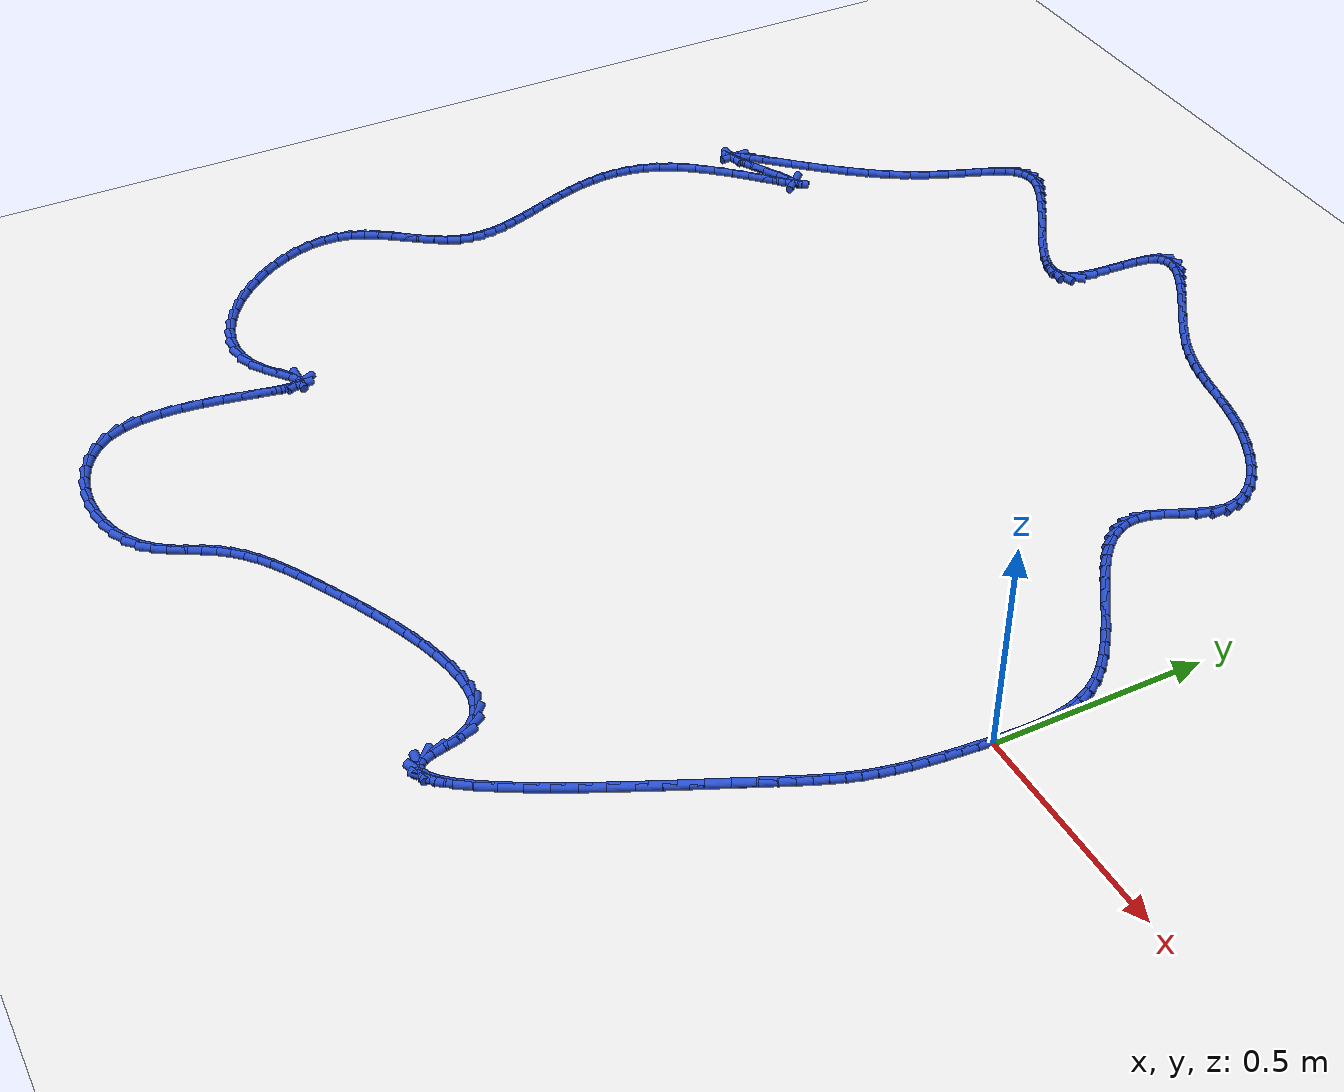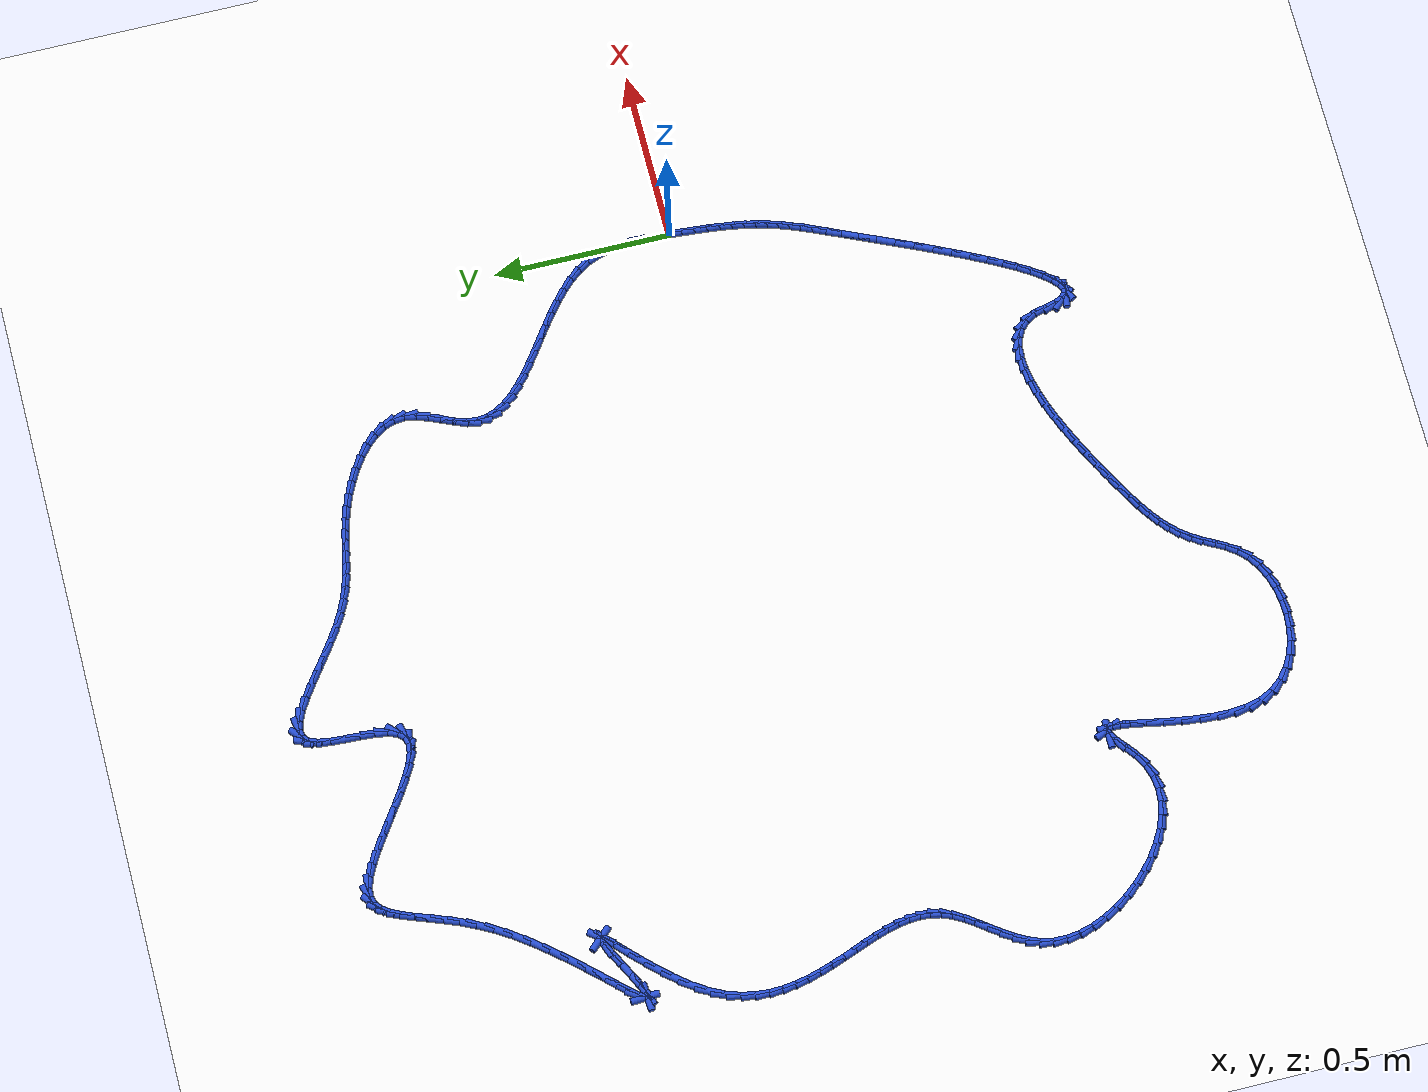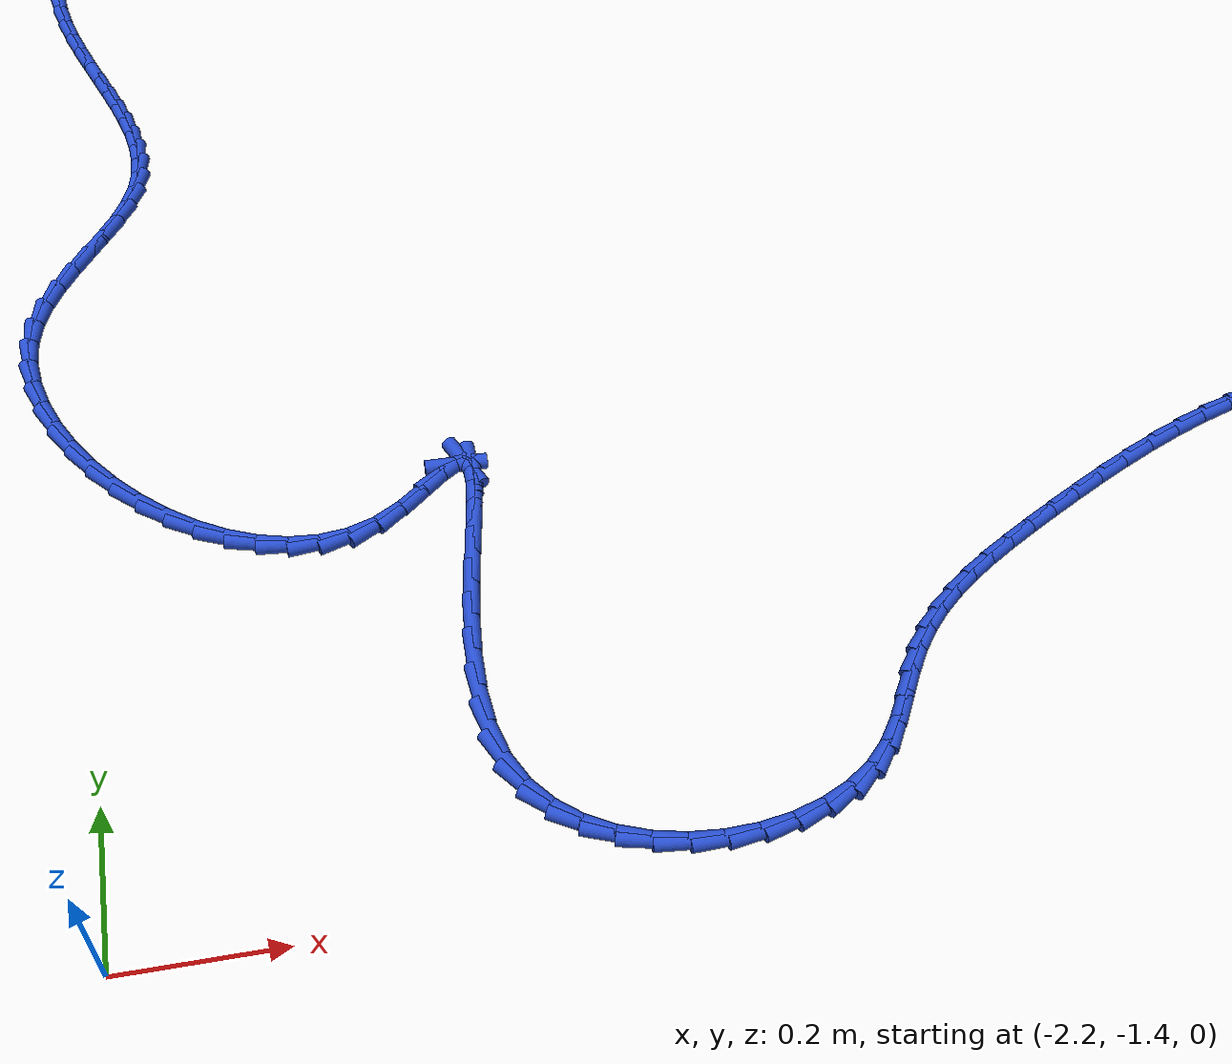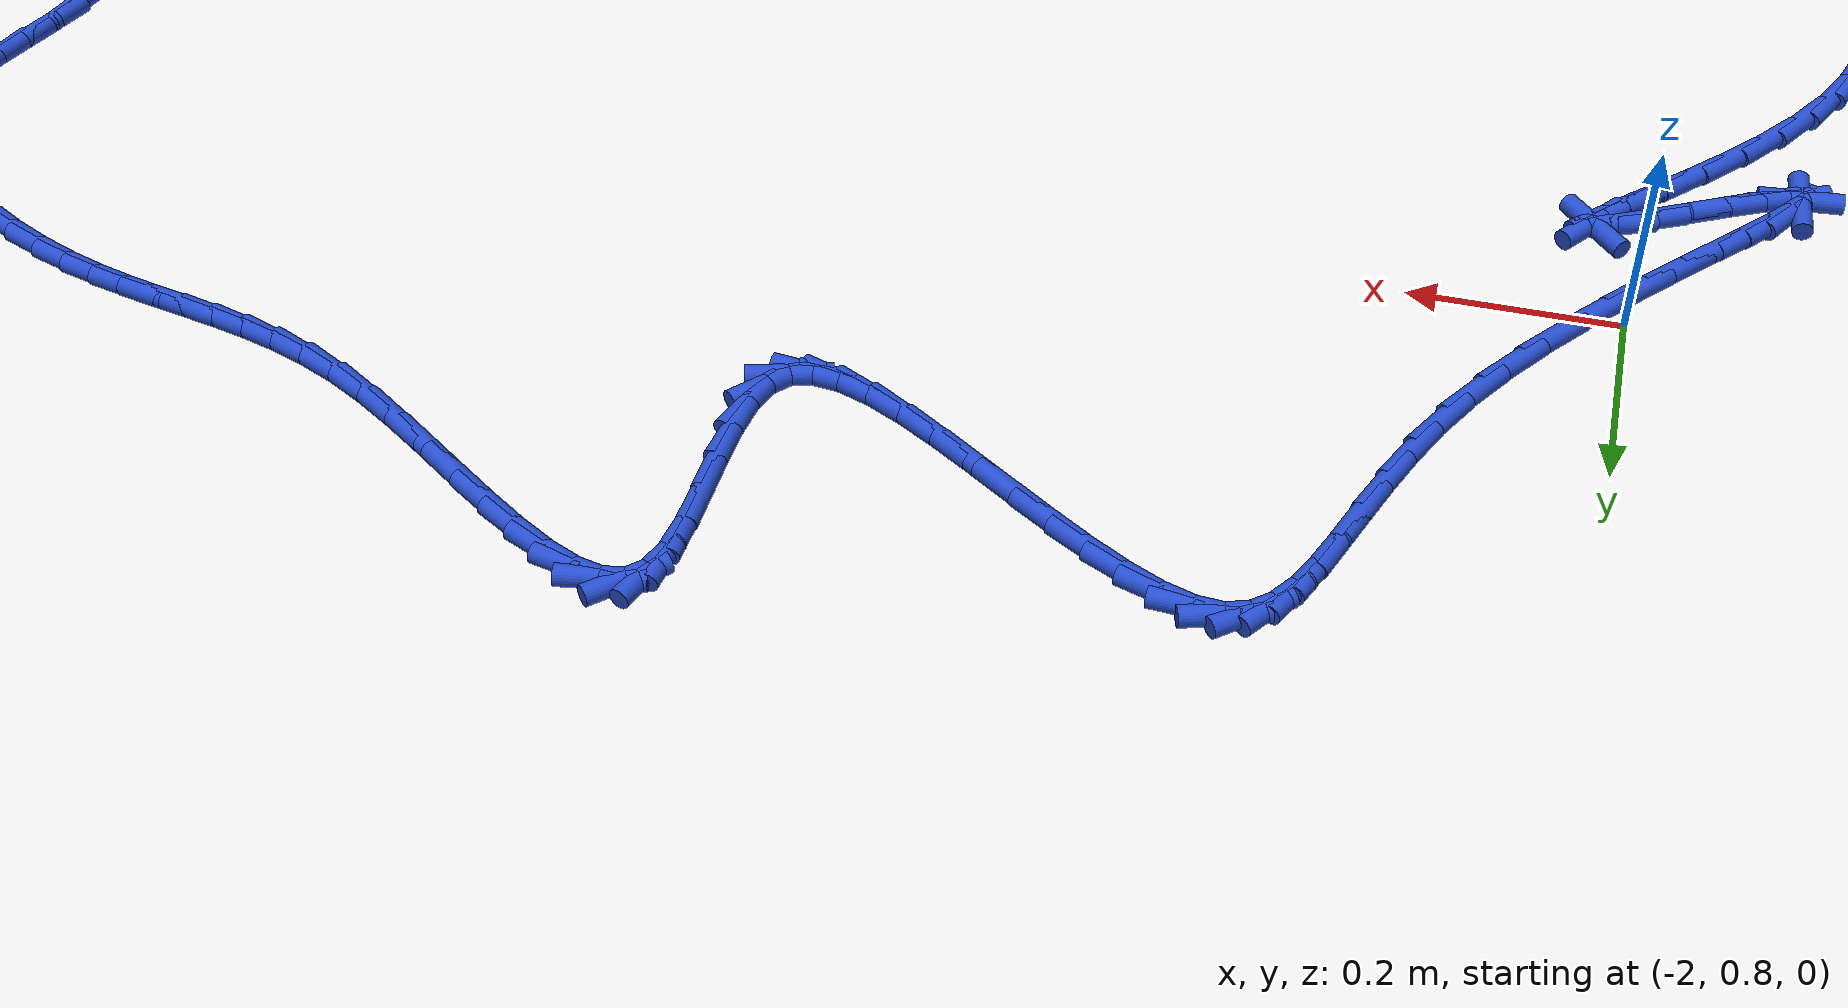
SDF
<sdf version="1.6">
 <world name="default">
  <light name="sun" type="directional">
   <pose>0 0 10 0 -0 0</pose>
   <diffuse>0.8 0.8 0.8 1</diffuse>
   <specular>0.2 0.2 0.2 1</specular>
   <attenuation>
    <range>1000</range>
    <constant>0.9</constant>
    <linear>0.01</linear>
    <quadratic>0.001</quadratic>
   </attenuation>
   <direction>-0.5 0.1 -0.9</direction>
  </light>
  <model name="ground_plane">
   <static>1</static>
   <link name="link">
    <collision name="collision">
     <geometry><plane><normal>0 0 1</normal><size>100 100</size></plane></geometry>
     <surface><friction><ode><mu>100</mu><mu2>50</mu2></ode></friction></surface>
    </collision>
    <visual name="visual">
     <cast_shadows>0</cast_shadows>
     <geometry><plane><normal>0 0 1</normal><size>100 100</size></plane></geometry>
     <material>
      <script><uri>file://media/materials/scripts/gazebo.material</uri><name>Gazebo/WhiteGlow</name></script>
     </material>
    </visual>
   </link>
  </model>
  <gravity>0 0 -9.8</gravity>
  <magnetic_field>6e-06 2.3e-05 -4.2e-05</magnetic_field>
  <atmosphere type="adiabatic"/>
  <physics name="default_physics" default="0" type="ode">
   <max_step_size>0.001</max_step_size>
   <real_time_factor>1</real_time_factor>
   <real_time_update_rate>1000</real_time_update_rate>
  </physics>
  <scene><ambient>0.4 0.4 0.4 1</ambient><background>0.7 0.7 0.7 1</background><shadows>1</shadows></scene>
  <spherical_coordinates>
   <surface_model>EARTH_WGS84</surface_model>
   <latitude_deg>0</latitude_deg>
   <longitude_deg>0</longitude_deg>
   <elevation>0</elevation>
   <heading_deg>0</heading_deg>
  </spherical_coordinates>
  <model name="line">
   <link name="link_0">
    <pose>2.168404344971009e-18 2.7755575615628914e-17 0.01 0 1.57 1.5134718039770452</pose>
    <collision name="collision">
     <geometry><cylinder><radius>0.01</radius><length>0.08</length></cylinder></geometry>
    </collision>
    <visual name="visual">
     <material>
      <script><name>Gazebo/Blue</name><uri>file://media/materials/scripts/gazebo.material</uri></script>
     </material>
     <geometry><cylinder><radius>0.01</radius><length>0.08</length></cylinder></geometry>
    </visual>
   </link>
   <link name="link_1">
    <pose>0.002078381581859288 0.036216690351167265 0.01 0 1.57 1.537497258225407</pose>
    <collision name="collision">
     <geometry><cylinder><radius>0.01</radius><length>0.08</length></cylinder></geometry>
    </collision>
    <visual name="visual">
     <material>
      <script><name>Gazebo/Blue</name><uri>file://media/materials/scripts/gazebo.material</uri></script>
     </material>
     <geometry><cylinder><radius>0.01</radius><length>0.08</length></cylinder></geometry>
    </visual>
   </link>
   <link name="link_2">
    <pose>0.0032791322106102364 0.07226294746520809 0.01 0 1.57 -1.5610327216190534</pose>
    <collision name="collision">
     <geometry><cylinder><radius>0.01</radius><length>0.08</length></cylinder></geometry>
    </collision>
    <visual name="visual">
     <material>
      <script><name>Gazebo/Blue</name><uri>file://media/materials/scripts/gazebo.material</uri></script>
     </material>
     <geometry><cylinder><radius>0.01</radius><length>0.08</length></cylinder></geometry>
    </visual>
   </link>
   <link name="link_3">
    <pose>0.0029313109725265948 0.10788607840744405 0.01 0 1.57 -1.4974650658319524</pose>
    <collision name="collision">
     <geometry><cylinder><radius>0.01</radius><length>0.08</length></cylinder></geometry>
    </collision>
    <visual name="visual">
     <material>
      <script><name>Gazebo/Blue</name><uri>file://media/materials/scripts/gazebo.material</uri></script>
     </material>
     <geometry><cylinder><radius>0.01</radius><length>0.08</length></cylinder></geometry>
    </visual>
   </link>
   <link name="link_4">
    <pose>0.000363976953882102 0.14283339024319658 0.01 0 1.57 -1.4117174796749625</pose>
    <collision name="collision">
     <geometry><cylinder><radius>0.01</radius><length>0.08</length></cylinder></geometry>
    </collision>
    <visual name="visual">
     <material>
      <script><name>Gazebo/Blue</name><uri>file://media/materials/scripts/gazebo.material</uri></script>
     </material>
     <geometry><cylinder><radius>0.01</radius><length>0.08</length></cylinder></geometry>
    </visual>
   </link>
   <link name="link_5">
    <pose>-0.0050938107590494976 0.1768521900377872 0.01 0 1.57 -1.3027459971653474</pose>
    <collision name="collision">
     <geometry><cylinder><radius>0.01</radius><length>0.08</length></cylinder></geometry>
    </collision>
    <visual name="visual">
     <material>
      <script><name>Gazebo/Blue</name><uri>file://media/materials/scripts/gazebo.material</uri></script>
     </material>
     <geometry><cylinder><radius>0.01</radius><length>0.08</length></cylinder></geometry>
    </visual>
   </link>
   <link name="link_6">
    <pose>-0.014112993079994467 0.20968978485653733 0.01 0 1.57 -1.1714922141252915</pose>
    <collision name="collision">
     <geometry><cylinder><radius>0.01</radius><length>0.08</length></cylinder></geometry>
    </collision>
    <visual name="visual">
     <material>
      <script><name>Gazebo/Blue</name><uri>file://media/materials/scripts/gazebo.material</uri></script>
     </material>
     <geometry><cylinder><radius>0.01</radius><length>0.08</length></cylinder></geometry>
    </visual>
   </link>
   <link name="link_7">
    <pose>-0.027364510922679053 0.2410934817647685 0.01 0 1.57 -1.0253797105672267</pose>
    <collision name="collision">
     <geometry><cylinder><radius>0.01</radius><length>0.08</length></cylinder></geometry>
    </collision>
    <visual name="visual">
     <material>
      <script><name>Gazebo/Blue</name><uri>file://media/materials/scripts/gazebo.material</uri></script>
     </material>
     <geometry><cylinder><radius>0.01</radius><length>0.08</length></cylinder></geometry>
    </visual>
   </link>
   <link name="link_8">
    <pose>-0.04541734272024359 0.2708435456552122 0.01 0 1.57 -0.8959484745496338</pose>
    <collision name="collision">
     <geometry><cylinder><radius>0.01</radius><length>0.08</length></cylinder></geometry>
    </collision>
    <visual name="visual">
     <material>
      <script><name>Gazebo/Blue</name><uri>file://media/materials/scripts/gazebo.material</uri></script>
     </material>
     <geometry><cylinder><radius>0.01</radius><length>0.08</length></cylinder></geometry>
    </visual>
   </link>
   <link name="link_9">
    <pose>-0.06795310005016525 0.29900706931562787 0.01 0 1.57 -0.7957365896403423</pose>
    <collision name="collision">
     <geometry><cylinder><radius>0.01</radius><length>0.08</length></cylinder></geometry>
    </collision>
    <visual name="visual">
     <material>
      <script><name>Gazebo/Blue</name><uri>file://media/materials/scripts/gazebo.material</uri></script>
     </material>
     <geometry><cylinder><radius>0.01</radius><length>0.08</length></cylinder></geometry>
    </visual>
   </link>
   <link name="link_10">
    <pose>-0.09419653071799564 0.3257988198278733 0.01 0 1.57 -0.720969327014609</pose>
    <collision name="collision">
     <geometry><cylinder><radius>0.01</radius><length>0.08</length></cylinder></geometry>
    </collision>
    <visual name="visual">
     <material>
      <script><name>Gazebo/Blue</name><uri>file://media/materials/scripts/gazebo.material</uri></script>
     </material>
     <geometry><cylinder><radius>0.01</radius><length>0.08</length></cylinder></geometry>
    </visual>
   </link>
   <link name="link_11">
    <pose>-0.12336860786261167 0.351434784377633 0.01 0 1.57 -0.6676697733295373</pose>
    <collision name="collision">
     <geometry><cylinder><radius>0.01</radius><length>0.08</length></cylinder></geometry>
    </collision>
    <visual name="visual">
     <material>
      <script><name>Gazebo/Blue</name><uri>file://media/materials/scripts/gazebo.material</uri></script>
     </material>
     <geometry><cylinder><radius>0.01</radius><length>0.08</length></cylinder></geometry>
    </visual>
   </link>
   <link name="link_12">
    <pose>-0.15469030462289043 0.376130950150592 0.01 0 1.57 -0.6327092212663911</pose>
    <collision name="collision">
     <geometry><cylinder><radius>0.01</radius><length>0.08</length></cylinder></geometry>
    </collision>
    <visual name="visual">
     <material>
      <script><name>Gazebo/Blue</name><uri>file://media/materials/scripts/gazebo.material</uri></script>
     </material>
     <geometry><cylinder><radius>0.01</radius><length>0.08</length></cylinder></geometry>
    </visual>
   </link>
   <link name="link_13">
    <pose>-0.18738259413770872 0.40010330433243485 0.01 0 1.57 -0.6140619857915841</pose>
    <collision name="collision">
     <geometry><cylinder><radius>0.01</radius><length>0.08</length></cylinder></geometry>
    </collision>
    <visual name="visual">
     <material>
      <script><name>Gazebo/Blue</name><uri>file://media/materials/scripts/gazebo.material</uri></script>
     </material>
     <geometry><cylinder><radius>0.01</radius><length>0.08</length></cylinder></geometry>
    </visual>
   </link>
   <link name="link_14">
    <pose>-0.2206664495459434 0.4235678341088464 0.01 0 1.57 -0.6108317376264476</pose>
    <collision name="collision">
     <geometry><cylinder><radius>0.01</radius><length>0.08</length></cylinder></geometry>
    </collision>
    <visual name="visual">
     <material>
      <script><name>Gazebo/Blue</name><uri>file://media/materials/scripts/gazebo.material</uri></script>
     </material>
     <geometry><cylinder><radius>0.01</radius><length>0.08</length></cylinder></geometry>
    </visual>
   </link>
   <link name="link_15">
    <pose>-0.25376284398647153 0.44674052666551156 0.01 0 1.57 -0.6232705815477121</pose>
    <collision name="collision">
     <geometry><cylinder><radius>0.01</radius><length>0.08</length></cylinder></geometry>
    </collision>
    <visual name="visual">
     <material>
      <script><name>Gazebo/Blue</name><uri>file://media/materials/scripts/gazebo.material</uri></script>
     </material>
     <geometry><cylinder><radius>0.01</radius><length>0.08</length></cylinder></geometry>
    </visual>
   </link>
   <link name="link_16">
    <pose>-0.28589275059817 0.46983736918811486 0.01 0 1.57 -0.6528851833674426</pose>
    <collision name="collision">
     <geometry><cylinder><radius>0.01</radius><length>0.08</length></cylinder></geometry>
    </collision>
    <visual name="visual">
     <material>
      <script><name>Gazebo/Blue</name><uri>file://media/materials/scripts/gazebo.material</uri></script>
     </material>
     <geometry><cylinder><radius>0.01</radius><length>0.08</length></cylinder></geometry>
    </visual>
   </link>
   <link name="link_17">
    <pose>-0.31627714251991573 0.4930743488623413 0.01 0 1.57 -0.7026622671491269</pose>
    <collision name="collision">
     <geometry><cylinder><radius>0.01</radius><length>0.08</length></cylinder></geometry>
    </collision>
    <visual name="visual">
     <material>
      <script><name>Gazebo/Blue</name><uri>file://media/materials/scripts/gazebo.material</uri></script>
     </material>
     <geometry><cylinder><radius>0.01</radius><length>0.08</length></cylinder></geometry>
    </visual>
   </link>
   <link name="link_18">
    <pose>-0.34413699289058575 0.5166674528738755 0.01 0 1.57 -0.7773717675324675</pose>
    <collision name="collision">
     <geometry><cylinder><radius>0.01</radius><length>0.08</length></cylinder></geometry>
    </collision>
    <visual name="visual">
     <material>
      <script><name>Gazebo/Blue</name><uri>file://media/materials/scripts/gazebo.material</uri></script>
     </material>
     <geometry><cylinder><radius>0.01</radius><length>0.08</length></cylinder></geometry>
    </visual>
   </link>
   <link name="link_19">
    <pose>-0.3686932748490567 0.5408326684084022 0.01 0 1.57 -0.8836919375241773</pose>
    <collision name="collision">
     <geometry><cylinder><radius>0.01</radius><length>0.08</length></cylinder></geometry>
    </collision>
    <visual name="visual">
     <material>
      <script><name>Gazebo/Blue</name><uri>file://media/materials/scripts/gazebo.material</uri></script>
     </material>
     <geometry><cylinder><radius>0.01</radius><length>0.08</length></cylinder></geometry>
    </visual>
   </link>
   <link name="link_20">
    <pose>-0.3891669615342059 0.5657859826516064 0.01 0 1.57 -1.0293117213981913</pose>
    <collision name="collision">
     <geometry><cylinder><radius>0.01</radius><length>0.08</length></cylinder></geometry>
    </collision>
    <visual name="visual">
     <material>
      <script><name>Gazebo/Blue</name><uri>file://media/materials/scripts/gazebo.material</uri></script>
     </material>
     <geometry><cylinder><radius>0.01</radius><length>0.08</length></cylinder></geometry>
    </visual>
   </link>
   <link name="link_21">
    <pose>-0.40477902608490995 0.5917433827891726 0.01 0 1.57 -1.2191458471171945</pose>
    <collision name="collision">
     <geometry><cylinder><radius>0.01</radius><length>0.08</length></cylinder></geometry>
    </collision>
    <visual name="visual">
     <material>
      <script><name>Gazebo/Blue</name><uri>file://media/materials/scripts/gazebo.material</uri></script>
     </material>
     <geometry><cylinder><radius>0.01</radius><length>0.08</length></cylinder></geometry>
    </visual>
   </link>
   <link name="link_22">
    <pose>-0.4147504416400459 0.6189208560067856 0.01 0 1.57 -1.4473000427369278</pose>
    <collision name="collision">
     <geometry><cylinder><radius>0.01</radius><length>0.08</length></cylinder></geometry>
    </collision>
    <visual name="visual">
     <material>
      <script><name>Gazebo/Blue</name><uri>file://media/materials/scripts/gazebo.material</uri></script>
     </material>
     <geometry><cylinder><radius>0.01</radius><length>0.08</length></cylinder></geometry>
    </visual>
   </link>
   <link name="link_23">
    <pose>-0.4183021813384908 0.6475343894901304 0.01 0 1.57 1.4511622171094867</pose>
    <collision name="collision">
     <geometry><cylinder><radius>0.01</radius><length>0.08</length></cylinder></geometry>
    </collision>
    <visual name="visual">
     <material>
      <script><name>Gazebo/Blue</name><uri>file://media/materials/scripts/gazebo.material</uri></script>
     </material>
     <geometry><cylinder><radius>0.01</radius><length>0.08</length></cylinder></geometry>
    </visual>
   </link>
   <link name="link_24">
    <pose>-0.41466422733661273 0.677798179427977 0.01 0 1.57 1.256721463330166</pose>
    <collision name="collision">
     <geometry><cylinder><radius>0.01</radius><length>0.08</length></cylinder></geometry>
    </collision>
    <visual name="visual">
     <material>
      <script><name>Gazebo/Blue</name><uri>file://media/materials/scripts/gazebo.material</uri></script>
     </material>
     <geometry><cylinder><radius>0.01</radius><length>0.08</length></cylinder></geometry>
    </visual>
   </link>
   <link name="link_25">
    <pose>-0.404308313295251 0.7096795612259761 0.01 0 1.57 1.1665611658719603</pose>
    <collision name="collision">
     <geometry><cylinder><radius>0.01</radius><length>0.08</length></cylinder></geometry>
    </collision>
    <visual name="visual">
     <material>
      <script><name>Gazebo/Blue</name><uri>file://media/materials/scripts/gazebo.material</uri></script>
     </material>
     <geometry><cylinder><radius>0.01</radius><length>0.08</length></cylinder></geometry>
    </visual>
   </link>
   <link name="link_26">
    <pose>-0.3902040466158815 0.7426492918153176 0.01 0 1.57 1.1598717814632624</pose>
    <collision name="collision">
     <geometry><cylinder><radius>0.01</radius><length>0.08</length></cylinder></geometry>
    </collision>
    <visual name="visual">
     <material>
      <script><name>Gazebo/Blue</name><uri>file://media/materials/scripts/gazebo.material</uri></script>
     </material>
     <geometry><cylinder><radius>0.01</radius><length>0.08</length></cylinder></geometry>
    </visual>
   </link>
   <link name="link_27">
    <pose>-0.3756204334847614 0.7761186075079607 0.01 0 1.57 1.2311646708894919</pose>
    <collision name="collision">
     <geometry><cylinder><radius>0.01</radius><length>0.08</length></cylinder></geometry>
    </collision>
    <visual name="visual">
     <material>
      <script><name>Gazebo/Blue</name><uri>file://media/materials/scripts/gazebo.material</uri></script>
     </material>
     <geometry><cylinder><radius>0.01</radius><length>0.08</length></cylinder></geometry>
    </visual>
   </link>
   <link name="link_28">
    <pose>-0.36382648008814805 0.8094987446158667 0.01 0 1.57 1.3971826716482925</pose>
    <collision name="collision">
     <geometry><cylinder><radius>0.01</radius><length>0.08</length></cylinder></geometry>
    </collision>
    <visual name="visual">
     <material>
      <script><name>Gazebo/Blue</name><uri>file://media/materials/scripts/gazebo.material</uri></script>
     </material>
     <geometry><cylinder><radius>0.01</radius><length>0.08</length></cylinder></geometry>
    </visual>
   </link>
   <link name="link_29">
    <pose>-0.35809119261229855 0.8422009394509945 0.01 0 1.57 -1.4765542553431965</pose>
    <collision name="collision">
     <geometry><cylinder><radius>0.01</radius><length>0.08</length></cylinder></geometry>
    </collision>
    <visual name="visual">
     <material>
      <script><name>Gazebo/Blue</name><uri>file://media/materials/scripts/gazebo.material</uri></script>
     </material>
     <geometry><cylinder><radius>0.01</radius><length>0.08</length></cylinder></geometry>
    </visual>
   </link>
   <link name="link_30">
    <pose>-0.36106757982778737 0.8736897457355649 0.01 0 1.57 -1.2087274826623706</pose>
    <collision name="collision">
     <geometry><cylinder><radius>0.01</radius><length>0.08</length></cylinder></geometry>
    </collision>
    <visual name="visual">
     <material>
      <script><name>Gazebo/Blue</name><uri>file://media/materials/scripts/gazebo.material</uri></script>
     </material>
     <geometry><cylinder><radius>0.01</radius><length>0.08</length></cylinder></geometry>
    </visual>
   </link>
   <link name="link_31">
    <pose>-0.37242974952171337 0.9036875547765354 0.01 0 1.57 -0.9913672337671484</pose>
    <collision name="collision">
     <geometry><cylinder><radius>0.01</radius><length>0.08</length></cylinder></geometry>
    </collision>
    <visual name="visual">
     <material>
      <script><name>Gazebo/Blue</name><uri>file://media/materials/scripts/gazebo.material</uri></script>
     </material>
     <geometry><cylinder><radius>0.01</radius><length>0.08</length></cylinder></geometry>
    </visual>
   </link>
   <link name="link_32">
    <pose>-0.39095253943699854 0.9319945938403321 0.01 0 1.57 -0.8238748802612862</pose>
    <collision name="collision">
     <geometry><cylinder><radius>0.01</radius><length>0.08</length></cylinder></geometry>
    </collision>
    <visual name="visual">
     <material>
      <script><name>Gazebo/Blue</name><uri>file://media/materials/scripts/gazebo.material</uri></script>
     </material>
     <geometry><cylinder><radius>0.01</radius><length>0.08</length></cylinder></geometry>
    </visual>
   </link>
   <link name="link_33">
    <pose>-0.41541059901301086 0.9584111064919211 0.01 0 1.57 -0.6951343314391202</pose>
    <collision name="collision">
     <geometry><cylinder><radius>0.01</radius><length>0.08</length></cylinder></geometry>
    </collision>
    <visual name="visual">
     <material>
      <script><name>Gazebo/Blue</name><uri>file://media/materials/scripts/gazebo.material</uri></script>
     </material>
     <geometry><cylinder><radius>0.01</radius><length>0.08</length></cylinder></geometry>
    </visual>
   </link>
   <link name="link_34">
    <pose>-0.4445785776891182 0.9827373362962682 0.01 0 1.57 -0.593659636820305</pose>
    <collision name="collision">
     <geometry><cylinder><radius>0.01</radius><length>0.08</length></cylinder></geometry>
    </collision>
    <visual name="visual">
     <material>
      <script><name>Gazebo/Blue</name><uri>file://media/materials/scripts/gazebo.material</uri></script>
     </material>
     <geometry><cylinder><radius>0.01</radius><length>0.08</length></cylinder></geometry>
    </visual>
   </link>
   <link name="link_35">
    <pose>-0.4772311249046881 1.0047735268183393 0.01 0 1.57 -0.510396871629072</pose>
    <collision name="collision">
     <geometry><cylinder><radius>0.01</radius><length>0.08</length></cylinder></geometry>
    </collision>
    <visual name="visual">
     <material>
      <script><name>Gazebo/Blue</name><uri>file://media/materials/scripts/gazebo.material</uri></script>
     </material>
     <geometry><cylinder><radius>0.01</radius><length>0.08</length></cylinder></geometry>
    </visual>
   </link>
   <link name="link_36">
    <pose>-0.5121428900990886 1.0243199216231007 0.01 0 1.57 -0.4385036709214673</pose>
    <collision name="collision">
     <geometry><cylinder><radius>0.01</radius><length>0.08</length></cylinder></geometry>
    </collision>
    <visual name="visual">
     <material>
      <script><name>Gazebo/Blue</name><uri>file://media/materials/scripts/gazebo.material</uri></script>
     </material>
     <geometry><cylinder><radius>0.01</radius><length>0.08</length></cylinder></geometry>
    </visual>
   </link>
   <link name="link_37">
    <pose>-0.5480885227116872 1.0411767642755172 0.01 0 1.57 -0.37242439723758225</pose>
    <collision name="collision">
     <geometry><cylinder><radius>0.01</radius><length>0.08</length></cylinder></geometry>
    </collision>
    <visual name="visual">
     <material>
      <script><name>Gazebo/Blue</name><uri>file://media/materials/scripts/gazebo.material</uri></script>
     </material>
     <geometry><cylinder><radius>0.01</radius><length>0.08</length></cylinder></geometry>
    </visual>
   </link>
   <link name="link_38">
    <pose>-0.5838426721818522 1.0551442983405557 0.01 0 1.57 -0.30881945779054787</pose>
    <collision name="collision">
     <geometry><cylinder><radius>0.01</radius><length>0.08</length></cylinder></geometry>
    </collision>
    <visual name="visual">
     <material>
      <script><name>Gazebo/Blue</name><uri>file://media/materials/scripts/gazebo.material</uri></script>
     </material>
     <geometry><cylinder><radius>0.01</radius><length>0.08</length></cylinder></geometry>
    </visual>
   </link>
   <link name="link_39">
    <pose>-0.6184028130059088 1.0661698928595957 0.01 0 1.57 -0.25520044645844464</pose>
    <collision name="collision">
     <geometry><cylinder><radius>0.01</radius><length>0.08</length></cylinder></geometry>
    </collision>
    <visual name="visual">
     <material>
      <script><name>Gazebo/Blue</name><uri>file://media/materials/scripts/gazebo.material</uri></script>
     </material>
     <geometry><cylinder><radius>0.01</radius><length>0.08</length></cylinder></geometry>
    </visual>
   </link>
   <link name="link_40">
    <pose>-0.6517987080443894 1.0748825095075163 0.01 0 1.57 -0.21838367436833178</pose>
    <collision name="collision">
     <geometry><cylinder><radius>0.01</radius><length>0.08</length></cylinder></geometry>
    </collision>
    <visual name="visual">
     <material>
      <script><name>Gazebo/Blue</name><uri>file://media/materials/scripts/gazebo.material</uri></script>
     </material>
     <geometry><cylinder><radius>0.01</radius><length>0.08</length></cylinder></geometry>
    </visual>
   </link>
   <link name="link_41">
    <pose>-0.6843588424780241 1.0821083483859455 0.01 0 1.57 -0.20203209034415978</pose>
    <collision name="collision">
     <geometry><cylinder><radius>0.01</radius><length>0.08</length></cylinder></geometry>
    </collision>
    <visual name="visual">
     <material>
      <script><name>Gazebo/Blue</name><uri>file://media/materials/scripts/gazebo.material</uri></script>
     </material>
     <geometry><cylinder><radius>0.01</radius><length>0.08</length></cylinder></geometry>
    </visual>
   </link>
   <link name="link_42">
    <pose>-0.7164117317384318 1.0886736295703712 0.01 0 1.57 -0.20811483407742346</pose>
    <collision name="collision">
     <geometry><cylinder><radius>0.01</radius><length>0.08</length></cylinder></geometry>
    </collision>
    <visual name="visual">
     <material>
      <script><name>Gazebo/Blue</name><uri>file://media/materials/scripts/gazebo.material</uri></script>
     </material>
     <geometry><cylinder><radius>0.01</radius><length>0.08</length></cylinder></geometry>
    </visual>
   </link>
   <link name="link_43">
    <pose>-0.7482858912572327 1.0954045731362827 0.01 0 1.57 -0.23663949010743343</pose>
    <collision name="collision">
     <geometry><cylinder><radius>0.01</radius><length>0.08</length></cylinder></geometry>
    </collision>
    <visual name="visual">
     <material>
      <script><name>Gazebo/Blue</name><uri>file://media/materials/scripts/gazebo.material</uri></script>
     </material>
     <geometry><cylinder><radius>0.01</radius><length>0.08</length></cylinder></geometry>
    </visual>
   </link>
   <link name="link_44">
    <pose>-0.7803098364660456 1.1031273991591677 0.01 0 1.57 -0.28552591077165795</pose>
    <collision name="collision">
     <geometry><cylinder><radius>0.01</radius><length>0.08</length></cylinder></geometry>
    </collision>
    <visual name="visual">
     <material>
      <script><name>Gazebo/Blue</name><uri>file://media/materials/scripts/gazebo.material</uri></script>
     </material>
     <geometry><cylinder><radius>0.01</radius><length>0.08</length></cylinder></geometry>
    </visual>
   </link>
   <link name="link_45">
    <pose>-0.8128120827964913 1.112668327714515 0.01 0 1.57 -0.35070169906277987</pose>
    <collision name="collision">
     <geometry><cylinder><radius>0.01</radius><length>0.08</length></cylinder></geometry>
    </collision>
    <visual name="visual">
     <material>
      <script><name>Gazebo/Blue</name><uri>file://media/materials/scripts/gazebo.material</uri></script>
     </material>
     <geometry><cylinder><radius>0.01</radius><length>0.08</length></cylinder></geometry>
    </visual>
   </link>
   <link name="link_46">
    <pose>-0.8461211456801883 1.1248535788778127 0.01 0 1.57 -0.42660946465348676</pose>
    <collision name="collision">
     <geometry><cylinder><radius>0.01</radius><length>0.08</length></cylinder></geometry>
    </collision>
    <visual name="visual">
     <material>
      <script><name>Gazebo/Blue</name><uri>file://media/materials/scripts/gazebo.material</uri></script>
     </material>
     <geometry><cylinder><radius>0.01</radius><length>0.08</length></cylinder></geometry>
    </visual>
   </link>
   <link name="link_47">
    <pose>-0.8805655405487569 1.1405093727245499 0.01 0 1.57 -0.5064786088960402</pose>
    <collision name="collision">
     <geometry><cylinder><radius>0.01</radius><length>0.08</length></cylinder></geometry>
    </collision>
    <visual name="visual">
     <material>
      <script><name>Gazebo/Blue</name><uri>file://media/materials/scripts/gazebo.material</uri></script>
     </material>
     <geometry><cylinder><radius>0.01</radius><length>0.08</length></cylinder></geometry>
    </visual>
   </link>
   <link name="link_48">
    <pose>-0.916454971192547 1.1604188410544227 0.01 0 1.57 -0.5700220450448398</pose>
    <collision name="collision">
     <geometry><cylinder><radius>0.01</radius><length>0.08</length></cylinder></geometry>
    </collision>
    <visual name="visual">
     <material>
      <script><name>Gazebo/Blue</name><uri>file://media/materials/scripts/gazebo.material</uri></script>
     </material>
     <geometry><cylinder><radius>0.01</radius><length>0.08</length></cylinder></geometry>
    </visual>
   </link>
   <link name="link_49">
    <pose>-0.953604222461999 1.1842314982718112 0.01 0 1.57 -0.606479181747917</pose>
    <collision name="collision">
     <geometry><cylinder><radius>0.01</radius><length>0.08</length></cylinder></geometry>
    </collision>
    <visual name="visual">
     <material>
      <script><name>Gazebo/Blue</name><uri>file://media/materials/scripts/gazebo.material</uri></script>
     </material>
     <geometry><cylinder><radius>0.01</radius><length>0.08</length></cylinder></geometry>
    </visual>
   </link>
   <link name="link_50">
    <pose>-0.9912958873776738 1.2103778674123125 0.01 0 1.57 -0.6215122622146935</pose>
    <collision name="collision">
     <geometry><cylinder><radius>0.01</radius><length>0.08</length></cylinder></geometry>
    </collision>
    <visual name="visual">
     <material>
      <script><name>Gazebo/Blue</name><uri>file://media/materials/scripts/gazebo.material</uri></script>
     </material>
     <geometry><cylinder><radius>0.01</radius><length>0.08</length></cylinder></geometry>
    </visual>
   </link>
   <link name="link_51">
    <pose>-1.028786280418254 1.2372282802159507 0.01 0 1.57 -0.6169969696944104</pose>
    <collision name="collision">
     <geometry><cylinder><radius>0.01</radius><length>0.08</length></cylinder></geometry>
    </collision>
    <visual name="visual">
     <material>
      <script><name>Gazebo/Blue</name><uri>file://media/materials/scripts/gazebo.material</uri></script>
     </material>
     <geometry><cylinder><radius>0.01</radius><length>0.08</length></cylinder></geometry>
    </visual>
   </link>
   <link name="link_52">
    <pose>-1.0653317160624214 1.2631530684227488 0.01 0 1.57 -0.5906124862228894</pose>
    <collision name="collision">
     <geometry><cylinder><radius>0.01</radius><length>0.08</length></cylinder></geometry>
    </collision>
    <visual name="visual">
     <material>
      <script><name>Gazebo/Blue</name><uri>file://media/materials/scripts/gazebo.material</uri></script>
     </material>
     <geometry><cylinder><radius>0.01</radius><length>0.08</length></cylinder></geometry>
    </visual>
   </link>
   <link name="link_53">
    <pose>-1.1001885087888583 1.2865225637727309 0.01 0 1.57 -0.5342708762013731</pose>
    <collision name="collision">
     <geometry><cylinder><radius>0.01</radius><length>0.08</length></cylinder></geometry>
    </collision>
    <visual name="visual">
     <material>
      <script><name>Gazebo/Blue</name><uri>file://media/materials/scripts/gazebo.material</uri></script>
     </material>
     <geometry><cylinder><radius>0.01</radius><length>0.08</length></cylinder></geometry>
    </visual>
   </link>
   <link name="link_54">
    <pose>-1.132612973076247 1.3057070980059202 0.01 0 1.57 -0.42875497078041486</pose>
    <collision name="collision">
     <geometry><cylinder><radius>0.01</radius><length>0.08</length></cylinder></geometry>
    </collision>
    <visual name="visual">
     <material>
      <script><name>Gazebo/Blue</name><uri>file://media/materials/scripts/gazebo.material</uri></script>
     </material>
     <geometry><cylinder><radius>0.01</radius><length>0.08</length></cylinder></geometry>
    </visual>
   </link>
   <link name="link_55">
    <pose>-1.1618614234032696 1.3190770028623402 0.01 0 1.57 -0.22981465669670645</pose>
    <collision name="collision">
     <geometry><cylinder><radius>0.01</radius><length>0.08</length></cylinder></geometry>
    </collision>
    <visual name="visual">
     <material>
      <script><name>Gazebo/Blue</name><uri>file://media/materials/scripts/gazebo.material</uri></script>
     </material>
     <geometry><cylinder><radius>0.01</radius><length>0.08</length></cylinder></geometry>
    </visual>
   </link>
   <link name="link_56">
    <pose>-1.1871901742486084 1.3250026100820147 0.01 0 1.57 0.1511869761358742</pose>
    <collision name="collision">
     <geometry><cylinder><radius>0.01</radius><length>0.08</length></cylinder></geometry>
    </collision>
    <visual name="visual">
     <material>
      <script><name>Gazebo/Blue</name><uri>file://media/materials/scripts/gazebo.material</uri></script>
     </material>
     <geometry><cylinder><radius>0.01</radius><length>0.08</length></cylinder></geometry>
    </visual>
   </link>
   <link name="link_57">
    <pose>-1.2078555400909454 1.321854251404967 0.01 0 1.57 0.7371158665554869</pose>
    <collision name="collision">
     <geometry><cylinder><radius>0.01</radius><length>0.08</length></cylinder></geometry>
    </collision>
    <visual name="visual">
     <material>
      <script><name>Gazebo/Blue</name><uri>file://media/materials/scripts/gazebo.material</uri></script>
     </material>
     <geometry><cylinder><radius>0.01</radius><length>0.08</length></cylinder></geometry>
    </visual>
   </link>
   <link name="link_58">
    <pose>-1.2231139341212829 1.3080024573017517 0.01 0 1.57 1.206753110256735</pose>
    <collision name="collision">
     <geometry><cylinder><radius>0.01</radius><length>0.08</length></cylinder></geometry>
    </collision>
    <visual name="visual">
     <material>
      <script><name>Gazebo/Blue</name><uri>file://media/materials/scripts/gazebo.material</uri></script>
     </material>
     <geometry><cylinder><radius>0.01</radius><length>0.08</length></cylinder></geometry>
    </visual>
   </link>
   <link name="link_59">
    <pose>-1.2327136593693917 1.2828080452623858 0.01 0 1.57 1.4149769873760727</pose>
    <collision name="collision">
     <geometry><cylinder><radius>0.01</radius><length>0.08</length></cylinder></geometry>
    </collision>
    <visual name="visual">
     <material>
      <script><name>Gazebo/Blue</name><uri>file://media/materials/scripts/gazebo.material</uri></script>
     </material>
     <geometry><cylinder><radius>0.01</radius><length>0.08</length></cylinder></geometry>
    </visual>
   </link>
   <link name="link_60">
    <pose>-1.2380370039415707 1.2489214193545006 0.01 0 1.57 1.5003813156631536</pose>
    <collision name="collision">
     <geometry><cylinder><radius>0.01</radius><length>0.08</length></cylinder></geometry>
    </collision>
    <visual name="visual">
     <material>
      <script><name>Gazebo/Blue</name><uri>file://media/materials/scripts/gazebo.material</uri></script>
     </material>
     <geometry><cylinder><radius>0.01</radius><length>0.08</length></cylinder></geometry>
    </visual>
   </link>
   <link name="link_61">
    <pose>-1.240805105815062 1.2096751661229674 0.01 0 1.57 1.5239722589209606</pose>
    <collision name="collision">
     <geometry><cylinder><radius>0.01</radius><length>0.08</length></cylinder></geometry>
    </collision>
    <visual name="visual">
     <material>
      <script><name>Gazebo/Blue</name><uri>file://media/materials/scripts/gazebo.material</uri></script>
     </material>
     <geometry><cylinder><radius>0.01</radius><length>0.08</length></cylinder></geometry>
    </visual>
   </link>
   <link name="link_62">
    <pose>-1.2427391029671067 1.1684018721126577 0.01 0 1.57 1.500330519350178</pose>
    <collision name="collision">
     <geometry><cylinder><radius>0.01</radius><length>0.08</length></cylinder></geometry>
    </collision>
    <visual name="visual">
     <material>
      <script><name>Gazebo/Blue</name><uri>file://media/materials/scripts/gazebo.material</uri></script>
     </material>
     <geometry><cylinder><radius>0.01</radius><length>0.08</length></cylinder></geometry>
    </visual>
   </link>
   <link name="link_63">
    <pose>-1.2455601333749464 1.128434123868443 0.01 0 1.57 1.4183163308471</pose>
    <collision name="collision">
     <geometry><cylinder><radius>0.01</radius><length>0.08</length></cylinder></geometry>
    </collision>
    <visual name="visual">
     <material>
      <script><name>Gazebo/Blue</name><uri>file://media/materials/scripts/gazebo.material</uri></script>
     </material>
     <geometry><cylinder><radius>0.01</radius><length>0.08</length></cylinder></geometry>
    </visual>
   </link>
   <link name="link_64">
    <pose>-1.2509893350158225 1.0931045079351944 0.01 0 1.57 1.2281784227628185</pose>
    <collision name="collision">
     <geometry><cylinder><radius>0.01</radius><length>0.08</length></cylinder></geometry>
    </collision>
    <visual name="visual">
     <material>
      <script><name>Gazebo/Blue</name><uri>file://media/materials/scripts/gazebo.material</uri></script>
     </material>
     <geometry><cylinder><radius>0.01</radius><length>0.08</length></cylinder></geometry>
    </visual>
   </link>
   <link name="link_65">
    <pose>-1.2607478458669774 1.0657456108577843 0.01 0 1.57 0.8130356119794419</pose>
    <collision name="collision">
     <geometry><cylinder><radius>0.01</radius><length>0.08</length></cylinder></geometry>
    </collision>
    <visual name="visual">
     <material>
      <script><name>Gazebo/Blue</name><uri>file://media/materials/scripts/gazebo.material</uri></script>
     </material>
     <geometry><cylinder><radius>0.01</radius><length>0.08</length></cylinder></geometry>
    </visual>
   </link>
   <link name="link_66">
    <pose>-1.2763374845315405 1.0492695318625107 0.01 0 1.57 0.2641855386854352</pose>
    <collision name="collision">
     <geometry><cylinder><radius>0.01</radius><length>0.08</length></cylinder></geometry>
    </collision>
    <visual name="visual">
     <material>
      <script><name>Gazebo/Blue</name><uri>file://media/materials/scripts/gazebo.material</uri></script>
     </material>
     <geometry><cylinder><radius>0.01</radius><length>0.08</length></cylinder></geometry>
    </visual>
   </link>
   <link name="link_67">
    <pose>-1.2976512958888897 1.0435039689364574 0.01 0 1.57 -0.1289506563340826</pose>
    <collision name="collision">
     <geometry><cylinder><radius>0.01</radius><length>0.08</length></cylinder></geometry>
    </collision>
    <visual name="visual">
     <material>
      <script><name>Gazebo/Blue</name><uri>file://media/materials/scripts/gazebo.material</uri></script>
     </material>
     <geometry><cylinder><radius>0.01</radius><length>0.08</length></cylinder></geometry>
    </visual>
   </link>
   <link name="link_68">
    <pose>-1.3238659883446862 1.0469032329491783 0.01 0 1.57 -0.34871070913643787</pose>
    <collision name="collision">
     <geometry><cylinder><radius>0.01</radius><length>0.08</length></cylinder></geometry>
    </collision>
    <visual name="visual">
     <material>
      <script><name>Gazebo/Blue</name><uri>file://media/materials/scripts/gazebo.material</uri></script>
     </material>
     <geometry><cylinder><radius>0.01</radius><length>0.08</length></cylinder></geometry>
    </visual>
   </link>
   <link name="link_69">
    <pose>-1.354154991300058 1.0579153481399222 0.01 0 1.57 -0.47088769487693266</pose>
    <collision name="collision">
     <geometry><cylinder><radius>0.01</radius><length>0.08</length></cylinder></geometry>
    </collision>
    <visual name="visual">
     <material>
      <script><name>Gazebo/Blue</name><uri>file://media/materials/scripts/gazebo.material</uri></script>
     </material>
     <geometry><cylinder><radius>0.01</radius><length>0.08</length></cylinder></geometry>
    </visual>
   </link>
   <link name="link_70">
    <pose>-1.387691734156133 1.074988338747939 0.01 0 1.57 -0.5405655522259198</pose>
    <collision name="collision">
     <geometry><cylinder><radius>0.01</radius><length>0.08</length></cylinder></geometry>
    </collision>
    <visual name="visual">
     <material>
      <script><name>Gazebo/Blue</name><uri>file://media/materials/scripts/gazebo.material</uri></script>
     </material>
     <geometry><cylinder><radius>0.01</radius><length>0.08</length></cylinder></geometry>
    </visual>
   </link>
   <link name="link_71">
    <pose>-1.4236496463140416 1.0965702290124792 0.01 0 1.57 -0.5787990562046467</pose>
    <collision name="collision">
     <geometry><cylinder><radius>0.01</radius><length>0.08</length></cylinder></geometry>
    </collision>
    <visual name="visual">
     <material>
      <script><name>Gazebo/Blue</name><uri>file://media/materials/scripts/gazebo.material</uri></script>
     </material>
     <geometry><cylinder><radius>0.01</radius><length>0.08</length></cylinder></geometry>
    </visual>
   </link>
   <link name="link_72">
    <pose>-1.461202157174911 1.121109043172792 0.01 0 1.57 -0.5951359262471945</pose>
    <collision name="collision">
     <geometry><cylinder><radius>0.01</radius><length>0.08</length></cylinder></geometry>
    </collision>
    <visual name="visual">
     <material>
      <script><name>Gazebo/Blue</name><uri>file://media/materials/scripts/gazebo.material</uri></script>
     </material>
     <geometry><cylinder><radius>0.01</radius><length>0.08</length></cylinder></geometry>
    </visual>
   </link>
   <link name="link_73">
    <pose>-1.4995226961398695 1.1470528054681268 0.01 0 1.57 -0.593208794557632</pose>
    <collision name="collision">
     <geometry><cylinder><radius>0.01</radius><length>0.08</length></cylinder></geometry>
    </collision>
    <visual name="visual">
     <material>
      <script><name>Gazebo/Blue</name><uri>file://media/materials/scripts/gazebo.material</uri></script>
     </material>
     <geometry><cylinder><radius>0.01</radius><length>0.08</length></cylinder></geometry>
    </visual>
   </link>
   <link name="link_74">
    <pose>-1.5377846926100471 1.1728495401377343 0.01 0 1.57 -0.5726565086281046</pose>
    <collision name="collision">
     <geometry><cylinder><radius>0.01</radius><length>0.08</length></cylinder></geometry>
    </collision>
    <visual name="visual">
     <material>
      <script><name>Gazebo/Blue</name><uri>file://media/materials/scripts/gazebo.material</uri></script>
     </material>
     <geometry><cylinder><radius>0.01</radius><length>0.08</length></cylinder></geometry>
    </visual>
   </link>
   <link name="link_75">
    <pose>-1.5751615759865714 1.1969472714208635 0.01 0 1.57 -0.5289537291684662</pose>
    <collision name="collision">
     <geometry><cylinder><radius>0.01</radius><length>0.08</length></cylinder></geometry>
    </collision>
    <visual name="visual">
     <material>
      <script><name>Gazebo/Blue</name><uri>file://media/materials/scripts/gazebo.material</uri></script>
     </material>
     <geometry><cylinder><radius>0.01</radius><length>0.08</length></cylinder></geometry>
    </visual>
   </link>
   <link name="link_76">
    <pose>-1.6108267756705714 1.2177940235567648 0.01 0 1.57 -0.4510191171223614</pose>
    <collision name="collision">
     <geometry><cylinder><radius>0.01</radius><length>0.08</length></cylinder></geometry>
    </collision>
    <visual name="visual">
     <material>
      <script><name>Gazebo/Blue</name><uri>file://media/materials/scripts/gazebo.material</uri></script>
     </material>
     <geometry><cylinder><radius>0.01</radius><length>0.08</length></cylinder></geometry>
    </visual>
   </link>
   <link name="link_77">
    <pose>-1.6439537210631752 1.2338378207846874 0.01 0 1.57 -0.3147234488270683</pose>
    <collision name="collision">
     <geometry><cylinder><radius>0.01</radius><length>0.08</length></cylinder></geometry>
    </collision>
    <visual name="visual">
     <material>
      <script><name>Gazebo/Blue</name><uri>file://media/materials/scripts/gazebo.material</uri></script>
     </material>
     <geometry><cylinder><radius>0.01</radius><length>0.08</length></cylinder></geometry>
    </visual>
   </link>
   <link name="link_78">
    <pose>-1.6737158415655125 1.243526687343882 0.01 0 1.57 -0.07005587584338384</pose>
    <collision name="collision">
     <geometry><cylinder><radius>0.01</radius><length>0.08</length></cylinder></geometry>
    </collision>
    <visual name="visual">
     <material>
      <script><name>Gazebo/Blue</name><uri>file://media/materials/scripts/gazebo.material</uri></script>
     </material>
     <geometry><cylinder><radius>0.01</radius><length>0.08</length></cylinder></geometry>
    </visual>
   </link>
   <link name="link_79">
    <pose>-1.699296269519936 1.2453216841003474 0.01 0 1.57 0.3082629461399176</pose>
    <collision name="collision">
     <geometry><cylinder><radius>0.01</radius><length>0.08</length></cylinder></geometry>
    </collision>
    <visual name="visual">
     <material>
      <script><name>Gazebo/Blue</name><uri>file://media/materials/scripts/gazebo.material</uri></script>
     </material>
     <geometry><cylinder><radius>0.01</radius><length>0.08</length></cylinder></geometry>
    </visual>
   </link>
   <link name="link_80">
    <pose>-1.720530532013136 1.2385604130201386 0.01 0 1.57 0.6863666119409795</pose>
    <collision name="collision">
     <geometry><cylinder><radius>0.01</radius><length>0.08</length></cylinder></geometry>
    </collision>
    <visual name="visual">
     <material>
      <script><name>Gazebo/Blue</name><uri>file://media/materials/scripts/gazebo.material</uri></script>
     </material>
     <geometry><cylinder><radius>0.01</radius><length>0.08</length></cylinder></geometry>
    </visual>
   </link>
   <link name="link_81">
    <pose>-1.7383079537936892 1.2239963319906033 0.01 0 1.57 0.9517958751249804</pose>
    <collision name="collision">
     <geometry><cylinder><radius>0.01</radius><length>0.08</length></cylinder></geometry>
    </collision>
    <visual name="visual">
     <material>
      <script><name>Gazebo/Blue</name><uri>file://media/materials/scripts/gazebo.material</uri></script>
     </material>
     <geometry><cylinder><radius>0.01</radius><length>0.08</length></cylinder></geometry>
    </visual>
   </link>
   <link name="link_82">
    <pose>-1.7536136756161138 1.2025116348645122 0.01 0 1.57 1.1054758057366276</pose>
    <collision name="collision">
     <geometry><cylinder><radius>0.01</radius><length>0.08</length></cylinder></geometry>
    </collision>
    <visual name="visual">
     <material>
      <script><name>Gazebo/Blue</name><uri>file://media/materials/scripts/gazebo.material</uri></script>
     </material>
     <geometry><cylinder><radius>0.01</radius><length>0.08</length></cylinder></geometry>
    </visual>
   </link>
   <link name="link_83">
    <pose>-1.767432838234926 1.1749885154946356 0.01 0 1.57 1.1838173204450204</pose>
    <collision name="collision">
     <geometry><cylinder><radius>0.01</radius><length>0.08</length></cylinder></geometry>
    </collision>
    <visual name="visual">
     <material>
      <script><name>Gazebo/Blue</name><uri>file://media/materials/scripts/gazebo.material</uri></script>
     </material>
     <geometry><cylinder><radius>0.01</radius><length>0.08</length></cylinder></geometry>
    </visual>
   </link>
   <link name="link_84">
    <pose>-1.7807505824046435 1.1423091677337438 0.01 0 1.57 1.2133561401373434</pose>
    <collision name="collision">
     <geometry><cylinder><radius>0.01</radius><length>0.08</length></cylinder></geometry>
    </collision>
    <visual name="visual">
     <material>
      <script><name>Gazebo/Blue</name><uri>file://media/materials/scripts/gazebo.material</uri></script>
     </material>
     <geometry><cylinder><radius>0.01</radius><length>0.08</length></cylinder></geometry>
    </visual>
   </link>
   <link name="link_85">
    <pose>-1.7945520488797828 1.105355785434608 0.01 0 1.57 1.2089680139124221</pose>
    <collision name="collision">
     <geometry><cylinder><radius>0.01</radius><length>0.08</length></cylinder></geometry>
    </collision>
    <visual name="visual">
     <material>
      <script><name>Gazebo/Blue</name><uri>file://media/materials/scripts/gazebo.material</uri></script>
     </material>
     <geometry><cylinder><radius>0.01</radius><length>0.08</length></cylinder></geometry>
    </visual>
   </link>
   <link name="link_86">
    <pose>-1.8098223784148617 1.0650105624499988 0.01 0 1.57 1.1786298504474582</pose>
    <collision name="collision">
     <geometry><cylinder><radius>0.01</radius><length>0.08</length></cylinder></geometry>
    </collision>
    <visual name="visual">
     <material>
      <script><name>Gazebo/Blue</name><uri>file://media/materials/scripts/gazebo.material</uri></script>
     </material>
     <geometry><cylinder><radius>0.01</radius><length>0.08</length></cylinder></geometry>
    </visual>
   </link>
   <link name="link_87">
    <pose>-1.8275467117643969 1.0221556926326862 0.01 0 1.57 1.1267176685425029</pose>
    <collision name="collision">
     <geometry><cylinder><radius>0.01</radius><length>0.08</length></cylinder></geometry>
    </collision>
    <visual name="visual">
     <material>
      <script><name>Gazebo/Blue</name><uri>file://media/materials/scripts/gazebo.material</uri></script>
     </material>
     <geometry><cylinder><radius>0.01</radius><length>0.08</length></cylinder></geometry>
    </visual>
   </link>
   <link name="link_88">
    <pose>-1.8487101896829055 0.977673369835442 0.01 0 1.57 1.0561657213988627</pose>
    <collision name="collision">
     <geometry><cylinder><radius>0.01</radius><length>0.08</length></cylinder></geometry>
    </collision>
    <visual name="visual">
     <material>
      <script><name>Gazebo/Blue</name><uri>file://media/materials/scripts/gazebo.material</uri></script>
     </material>
     <geometry><cylinder><radius>0.01</radius><length>0.08</length></cylinder></geometry>
    </visual>
   </link>
   <link name="link_89">
    <pose>-1.8742849130809207 0.932444714597224 0.01 0 1.57 0.9830092596405903</pose>
    <collision name="collision">
     <geometry><cylinder><radius>0.01</radius><length>0.08</length></cylinder></geometry>
    </collision>
    <visual name="visual">
     <material>
      <script><name>Gazebo/Blue</name><uri>file://media/materials/scripts/gazebo.material</uri></script>
     </material>
     <geometry><cylinder><radius>0.01</radius><length>0.08</length></cylinder></geometry>
    </visual>
   </link>
   <link name="link_90">
    <pose>-1.9043807460078594 0.8872798764597365 0.01 0 1.57 0.926738214381568</pose>
    <collision name="collision">
     <geometry><cylinder><radius>0.01</radius><length>0.08</length></cylinder></geometry>
    </collision>
    <visual name="visual">
     <material>
      <script><name>Gazebo/Blue</name><uri>file://media/materials/scripts/gazebo.material</uri></script>
     </material>
     <geometry><cylinder><radius>0.01</radius><length>0.08</length></cylinder></geometry>
    </visual>
   </link>
   <link name="link_91">
    <pose>-1.9377230323457544 0.8428750446581464 0.01 0 1.57 0.884495642762522</pose>
    <collision name="collision">
     <geometry><cylinder><radius>0.01</radius><length>0.08</length></cylinder></geometry>
    </collision>
    <visual name="visual">
     <material>
      <script><name>Gazebo/Blue</name><uri>file://media/materials/scripts/gazebo.material</uri></script>
     </material>
     <geometry><cylinder><radius>0.01</radius><length>0.08</length></cylinder></geometry>
    </visual>
   </link>
   <link name="link_92">
    <pose>-1.9729122185356147 0.7999161280785155 0.01 0 1.57 0.853176916357269</pose>
    <collision name="collision">
     <geometry><cylinder><radius>0.01</radius><length>0.08</length></cylinder></geometry>
    </collision>
    <visual name="visual">
     <material>
      <script><name>Gazebo/Blue</name><uri>file://media/materials/scripts/gazebo.material</uri></script>
     </material>
     <geometry><cylinder><radius>0.01</radius><length>0.08</length></cylinder></geometry>
    </visual>
   </link>
   <link name="link_93">
    <pose>-2.0085487510184477 0.7590890356069045 0.01 0 1.57 0.831106649978659</pose>
    <collision name="collision">
     <geometry><cylinder><radius>0.01</radius><length>0.08</length></cylinder></geometry>
    </collision>
    <visual name="visual">
     <material>
      <script><name>Gazebo/Blue</name><uri>file://media/materials/scripts/gazebo.material</uri></script>
     </material>
     <geometry><cylinder><radius>0.01</radius><length>0.08</length></cylinder></geometry>
    </visual>
   </link>
   <link name="link_94">
    <pose>-2.0432330762352637 0.7210796761293755 0.01 0 1.57 0.8179003141819051</pose>
    <collision name="collision">
     <geometry><cylinder><radius>0.01</radius><length>0.08</length></cylinder></geometry>
    </collision>
    <visual name="visual">
     <material>
      <script><name>Gazebo/Blue</name><uri>file://media/materials/scripts/gazebo.material</uri></script>
     </material>
     <geometry><cylinder><radius>0.01</radius><length>0.08</length></cylinder></geometry>
    </visual>
   </link>
   <link name="link_95">
    <pose>-2.0755656406270684 0.686573958531989 0.01 0 1.57 0.8148462340817876</pose>
    <collision name="collision">
     <geometry><cylinder><radius>0.01</radius><length>0.08</length></cylinder></geometry>
    </collision>
    <visual name="visual">
     <material>
      <script><name>Gazebo/Blue</name><uri>file://media/materials/scripts/gazebo.material</uri></script>
     </material>
     <geometry><cylinder><radius>0.01</radius><length>0.08</length></cylinder></geometry>
    </visual>
   </link>
   <link name="link_96">
    <pose>-2.1041468906348713 0.6562577917008064 0.01 0 1.57 0.8265102482317889</pose>
    <collision name="collision">
     <geometry><cylinder><radius>0.01</radius><length>0.08</length></cylinder></geometry>
    </collision>
    <visual name="visual">
     <material>
      <script><name>Gazebo/Blue</name><uri>file://media/materials/scripts/gazebo.material</uri></script>
     </material>
     <geometry><cylinder><radius>0.01</radius><length>0.08</length></cylinder></geometry>
    </visual>
   </link>
   <link name="link_97">
    <pose>-2.1275772726996816 0.6308170845218893 0.01 0 1.57 0.8668128864565462</pose>
    <collision name="collision">
     <geometry><cylinder><radius>0.01</radius><length>0.08</length></cylinder></geometry>
    </collision>
    <visual name="visual">
     <material>
      <script><name>Gazebo/Blue</name><uri>file://media/materials/scripts/gazebo.material</uri></script>
     </material>
     <geometry><cylinder><radius>0.01</radius><length>0.08</length></cylinder></geometry>
    </visual>
   </link>
   <link name="link_98">
    <pose>-2.144457233262506 0.6109377458812988 0.01 0 1.57 0.9908636120371687</pose>
    <collision name="collision">
     <geometry><cylinder><radius>0.01</radius><length>0.08</length></cylinder></geometry>
    </collision>
    <visual name="visual">
     <material>
      <script><name>Gazebo/Blue</name><uri>file://media/materials/scripts/gazebo.material</uri></script>
     </material>
     <geometry><cylinder><radius>0.01</radius><length>0.08</length></cylinder></geometry>
    </visual>
   </link>
   <link name="link_99">
    <pose>-2.153387218764354 0.5973056846650964 0.01 0 1.57 -1.5082491265928677</pose>
    <collision name="collision">
     <geometry><cylinder><radius>0.01</radius><length>0.08</length></cylinder></geometry>
    </collision>
    <visual name="visual">
     <material>
      <script><name>Gazebo/Blue</name><uri>file://media/materials/scripts/gazebo.material</uri></script>
     </material>
     <geometry><cylinder><radius>0.01</radius><length>0.08</length></cylinder></geometry>
    </visual>
   </link>
   <link name="link_100">
    <pose>-2.1529676756462335 0.5906068097593429 0.01 0 1.57 0.08220764440624673</pose>
    <collision name="collision">
     <geometry><cylinder><radius>0.01</radius><length>0.08</length></cylinder></geometry>
    </collision>
    <visual name="visual">
     <material>
      <script><name>Gazebo/Blue</name><uri>file://media/materials/scripts/gazebo.material</uri></script>
     </material>
     <geometry><cylinder><radius>0.01</radius><length>0.08</length></cylinder></geometry>
    </visual>
   </link>
   <link name="link_101">
    <pose>-2.141799050349153 0.5915270300501001 0.01 0 1.57 0.3752202910953797</pose>
    <collision name="collision">
     <geometry><cylinder><radius>0.01</radius><length>0.08</length></cylinder></geometry>
    </collision>
    <visual name="visual">
     <material>
      <script><name>Gazebo/Blue</name><uri>file://media/materials/scripts/gazebo.material</uri></script>
     </material>
     <geometry><cylinder><radius>0.01</radius><length>0.08</length></cylinder></geometry>
    </visual>
   </link>
   <link name="link_102">
    <pose>-2.1186578517103585 0.6006419090064952 0.01 0 1.57 0.446023096392137</pose>
    <collision name="collision">
     <geometry><cylinder><radius>0.01</radius><length>0.08</length></cylinder></geometry>
    </collision>
    <visual name="visual">
     <material>
      <script><name>Gazebo/Blue</name><uri>file://media/materials/scripts/gazebo.material</uri></script>
     </material>
     <geometry><cylinder><radius>0.01</radius><length>0.08</length></cylinder></geometry>
    </visual>
   </link>
   <link name="link_103">
    <pose>-2.085753677818937 0.6163753543610477 0.01 0 1.57 0.4668876714107639</pose>
    <collision name="collision">
     <geometry><cylinder><radius>0.01</radius><length>0.08</length></cylinder></geometry>
    </collision>
    <visual name="visual">
     <material>
      <script><name>Gazebo/Blue</name><uri>file://media/materials/scripts/gazebo.material</uri></script>
     </material>
     <geometry><cylinder><radius>0.01</radius><length>0.08</length></cylinder></geometry>
    </visual>
   </link>
   <link name="link_104">
    <pose>-2.0484181482259043 0.6351945768612597 0.01 0 1.57 0.4667301630912546</pose>
    <collision name="collision">
     <geometry><cylinder><radius>0.01</radius><length>0.08</length></cylinder></geometry>
    </collision>
    <visual name="visual">
     <material>
      <script><name>Gazebo/Blue</name><uri>file://media/materials/scripts/gazebo.material</uri></script>
     </material>
     <geometry><cylinder><radius>0.01</radius><length>0.08</length></cylinder></geometry>
    </visual>
   </link>
   <link name="link_105">
    <pose>-2.0120965553306003 0.6534955438880202 0.01 0 1.57 0.44328592333842437</pose>
    <collision name="collision">
     <geometry><cylinder><radius>0.01</radius><length>0.08</length></cylinder></geometry>
    </collision>
    <visual name="visual">
     <material>
      <script><name>Gazebo/Blue</name><uri>file://media/materials/scripts/gazebo.material</uri></script>
     </material>
     <geometry><cylinder><radius>0.01</radius><length>0.08</length></cylinder></geometry>
    </visual>
   </link>
   <link name="link_106">
    <pose>-1.98223419153236 0.6676742228222183 0.01 0 1.57 0.34515678373902464</pose>
    <collision name="collision">
     <geometry><cylinder><radius>0.01</radius><length>0.08</length></cylinder></geometry>
    </collision>
    <visual name="visual">
     <material>
      <script><name>Gazebo/Blue</name><uri>file://media/materials/scripts/gazebo.material</uri></script>
     </material>
     <geometry><cylinder><radius>0.01</radius><length>0.08</length></cylinder></geometry>
    </visual>
   </link>
   <link name="link_107">
    <pose>-1.96425828899957 0.6741374510950087 0.01 0 1.57 -0.8190024644762359</pose>
    <collision name="collision">
     <geometry><cylinder><radius>0.01</radius><length>0.08</length></cylinder></geometry>
    </collision>
    <visual name="visual">
     <material>
      <script><name>Gazebo/Blue</name><uri>file://media/materials/scripts/gazebo.material</uri></script>
     </material>
     <geometry><cylinder><radius>0.01</radius><length>0.08</length></cylinder></geometry>
    </visual>
   </link>
   <link name="link_108">
    <pose>-1.961120921755447 0.6707818086291352 0.01 0 1.57 0.9033847684411322</pose>
    <collision name="collision">
     <geometry><cylinder><radius>0.01</radius><length>0.08</length></cylinder></geometry>
    </collision>
    <visual name="visual">
     <material>
      <script><name>Gazebo/Blue</name><uri>file://media/materials/scripts/gazebo.material</uri></script>
     </material>
     <geometry><cylinder><radius>0.01</radius><length>0.08</length></cylinder></geometry>
    </visual>
   </link>
   <link name="link_109">
    <pose>-1.9708026607555613 0.6584961121793144 0.01 0 1.57 0.7874638761017827</pose>
    <collision name="collision">
     <geometry><cylinder><radius>0.01</radius><length>0.08</length></cylinder></geometry>
    </collision>
    <visual name="visual">
     <material>
      <script><name>Gazebo/Blue</name><uri>file://media/materials/scripts/gazebo.material</uri></script>
     </material>
     <geometry><cylinder><radius>0.01</radius><length>0.08</length></cylinder></geometry>
    </visual>
   </link>
   <link name="link_110">
    <pose>-1.9906892530007978 0.6385271897740209 0.01 0 1.57 0.7655080218928605</pose>
    <collision name="collision">
     <geometry><cylinder><radius>0.01</radius><length>0.08</length></cylinder></geometry>
    </collision>
    <visual name="visual">
     <material>
      <script><name>Gazebo/Blue</name><uri>file://media/materials/scripts/gazebo.material</uri></script>
     </material>
     <geometry><cylinder><radius>0.01</radius><length>0.08</length></cylinder></geometry>
    </visual>
   </link>
   <link name="link_111">
    <pose>-2.0181664454920427 0.6121218694417302 0.01 0 1.57 0.771992712674088</pose>
    <collision name="collision">
     <geometry><cylinder><radius>0.01</radius><length>0.08</length></cylinder></geometry>
    </collision>
    <visual name="visual">
     <material>
      <script><name>Gazebo/Blue</name><uri>file://media/materials/scripts/gazebo.material</uri></script>
     </material>
     <geometry><cylinder><radius>0.01</radius><length>0.08</length></cylinder></geometry>
    </visual>
   </link>
   <link name="link_112">
    <pose>-2.0506199852301825 0.580526979210918 0.01 0 1.57 0.7956602707618387</pose>
    <collision name="collision">
     <geometry><cylinder><radius>0.01</radius><length>0.08</length></cylinder></geometry>
    </collision>
    <visual name="visual">
     <material>
      <script><name>Gazebo/Blue</name><uri>file://media/materials/scripts/gazebo.material</uri></script>
     </material>
     <geometry><cylinder><radius>0.01</radius><length>0.08</length></cylinder></geometry>
    </visual>
   </link>
   <link name="link_113">
    <pose>-2.085435619216101 0.5449893471100591 0.01 0 1.57 0.8357706373599532</pose>
    <collision name="collision">
     <geometry><cylinder><radius>0.01</radius><length>0.08</length></cylinder></geometry>
    </collision>
    <visual name="visual">
     <material>
      <script><name>Gazebo/Blue</name><uri>file://media/materials/scripts/gazebo.material</uri></script>
     </material>
     <geometry><cylinder><radius>0.01</radius><length>0.08</length></cylinder></geometry>
    </visual>
   </link>
   <link name="link_114">
    <pose>-2.119999094450685 0.506755801167629 0.01 0 1.57 0.8968094082175065</pose>
    <collision name="collision">
     <geometry><cylinder><radius>0.01</radius><length>0.08</length></cylinder></geometry>
    </collision>
    <visual name="visual">
     <material>
      <script><name>Gazebo/Blue</name><uri>file://media/materials/scripts/gazebo.material</uri></script>
     </material>
     <geometry><cylinder><radius>0.01</radius><length>0.08</length></cylinder></geometry>
    </visual>
   </link>
   <link name="link_115">
    <pose>-2.151696157934821 0.4670731694121031 0.01 0 1.57 0.9887843377597655</pose>
    <collision name="collision">
     <geometry><cylinder><radius>0.01</radius><length>0.08</length></cylinder></geometry>
    </collision>
    <visual name="visual">
     <material>
      <script><name>Gazebo/Blue</name><uri>file://media/materials/scripts/gazebo.material</uri></script>
     </material>
     <geometry><cylinder><radius>0.01</radius><length>0.08</length></cylinder></geometry>
    </visual>
   </link>
   <link name="link_116">
    <pose>-2.1779523535140695 0.4271730396819369 0.01 0 1.57 1.108790935771907</pose>
    <collision name="collision">
     <geometry><cylinder><radius>0.01</radius><length>0.08</length></cylinder></geometry>
    </collision>
    <visual name="visual">
     <material>
      <script><name>Gazebo/Blue</name><uri>file://media/materials/scripts/gazebo.material</uri></script>
     </material>
     <geometry><cylinder><radius>0.01</radius><length>0.08</length></cylinder></geometry>
    </visual>
   </link>
   <link name="link_117">
    <pose>-2.197580071598372 0.3877559073297062 0.01 0 1.57 1.2360905210885276</pose>
    <collision name="collision">
     <geometry><cylinder><radius>0.01</radius><length>0.08</length></cylinder></geometry>
    </collision>
    <visual name="visual">
     <material>
      <script><name>Gazebo/Blue</name><uri>file://media/materials/scripts/gazebo.material</uri></script>
     </material>
     <geometry><cylinder><radius>0.01</radius><length>0.08</length></cylinder></geometry>
    </visual>
   </link>
   <link name="link_118">
    <pose>-2.211105677305088 0.3488659015954834 0.01 0 1.57 1.3637909322514807</pose>
    <collision name="collision">
     <geometry><cylinder><radius>0.01</radius><length>0.08</length></cylinder></geometry>
    </collision>
    <visual name="visual">
     <material>
      <script><name>Gazebo/Blue</name><uri>file://media/materials/scripts/gazebo.material</uri></script>
     </material>
     <geometry><cylinder><radius>0.01</radius><length>0.08</length></cylinder></geometry>
    </visual>
   </link>
   <link name="link_119">
    <pose>-2.219161679486924 0.3105065040069609 0.01 0 1.57 1.4859015579453456</pose>
    <collision name="collision">
     <geometry><cylinder><radius>0.01</radius><length>0.08</length></cylinder></geometry>
    </collision>
    <visual name="visual">
     <material>
      <script><name>Gazebo/Blue</name><uri>file://media/materials/scripts/gazebo.material</uri></script>
     </material>
     <geometry><cylinder><radius>0.01</radius><length>0.08</length></cylinder></geometry>
    </visual>
   </link>
   <link name="link_120">
    <pose>-2.2223805869965867 0.27268119609183133 0.01 0 1.57 -1.5443680985564807</pose>
    <collision name="collision">
     <geometry><cylinder><radius>0.01</radius><length>0.08</length></cylinder></geometry>
    </collision>
    <visual name="visual">
     <material>
      <script><name>Gazebo/Blue</name><uri>file://media/materials/scripts/gazebo.material</uri></script>
     </material>
     <geometry><cylinder><radius>0.01</radius><length>0.08</length></cylinder></geometry>
    </visual>
   </link>
   <link name="link_121">
    <pose>-2.2213949086867792 0.23539345937778564 0.01 0 1.57 -1.447394805990771</pose>
    <collision name="collision">
     <geometry><cylinder><radius>0.01</radius><length>0.08</length></cylinder></geometry>
    </collision>
    <visual name="visual">
     <material>
      <script><name>Gazebo/Blue</name><uri>file://media/materials/scripts/gazebo.material</uri></script>
     </material>
     <geometry><cylinder><radius>0.01</radius><length>0.08</length></cylinder></geometry>
    </visual>
   </link>
   <link name="link_122">
    <pose>-2.2168371534102094 0.19864677539251685 0.01 0 1.57 -1.3665870144497916</pose>
    <collision name="collision">
     <geometry><cylinder><radius>0.01</radius><length>0.08</length></cylinder></geometry>
    </collision>
    <visual name="visual">
     <material>
      <script><name>Gazebo/Blue</name><uri>file://media/materials/scripts/gazebo.material</uri></script>
     </material>
     <geometry><cylinder><radius>0.01</radius><length>0.08</length></cylinder></geometry>
    </visual>
   </link>
   <link name="link_123">
    <pose>-2.2093398300195815 0.16244462566371676 0.01 0 1.57 -1.302443262651336</pose>
    <collision name="collision">
     <geometry><cylinder><radius>0.01</radius><length>0.08</length></cylinder></geometry>
    </collision>
    <visual name="visual">
     <material>
      <script><name>Gazebo/Blue</name><uri>file://media/materials/scripts/gazebo.material</uri></script>
     </material>
     <geometry><cylinder><radius>0.01</radius><length>0.08</length></cylinder></geometry>
    </visual>
   </link>
   <link name="link_124">
    <pose>-2.1995354473676008 0.12679049171907772 0.01 0 1.57 -1.2547470159617584</pose>
    <collision name="collision">
     <geometry><cylinder><radius>0.01</radius><length>0.08</length></cylinder></geometry>
    </collision>
    <visual name="visual">
     <material>
      <script><name>Gazebo/Blue</name><uri>file://media/materials/scripts/gazebo.material</uri></script>
     </material>
     <geometry><cylinder><radius>0.01</radius><length>0.08</length></cylinder></geometry>
    </visual>
   </link>
   <link name="link_125">
    <pose>-2.1880565143069735 0.09168785508629192 0.01 0 1.57 -1.2230946129520144</pose>
    <collision name="collision">
     <geometry><cylinder><radius>0.01</radius><length>0.08</length></cylinder></geometry>
    </collision>
    <visual name="visual">
     <material>
      <script><name>Gazebo/Blue</name><uri>file://media/materials/scripts/gazebo.material</uri></script>
     </material>
     <geometry><cylinder><radius>0.01</radius><length>0.08</length></cylinder></geometry>
    </visual>
   </link>
   <link name="link_126">
    <pose>-2.175535539690405 0.057140197293051406 0.01 0 1.57 -1.20727370632932</pose>
    <collision name="collision">
     <geometry><cylinder><radius>0.01</radius><length>0.08</length></cylinder></geometry>
    </collision>
    <visual name="visual">
     <material>
      <script><name>Gazebo/Blue</name><uri>file://media/materials/scripts/gazebo.material</uri></script>
     </material>
     <geometry><cylinder><radius>0.01</radius><length>0.08</length></cylinder></geometry>
    </visual>
   </link>
   <link name="link_127">
    <pose>-2.1626050323706005 0.02315099986704846 0.01 0 1.57 -1.2075140687145731</pose>
    <collision name="collision">
     <geometry><cylinder><radius>0.01</radius><length>0.08</length></cylinder></geometry>
    </collision>
    <visual name="visual">
     <material>
      <script><name>Gazebo/Blue</name><uri>file://media/materials/scripts/gazebo.material</uri></script>
     </material>
     <geometry><cylinder><radius>0.01</radius><length>0.08</length></cylinder></geometry>
    </visual>
   </link>
   <link name="link_128">
    <pose>-2.1498975012002663 -0.01027625566402482 0.01 0 1.57 -1.224653957996939</pose>
    <collision name="collision">
     <geometry><cylinder><radius>0.01</radius><length>0.08</length></cylinder></geometry>
    </collision>
    <visual name="visual">
     <material>
      <script><name>Gazebo/Blue</name><uri>file://media/materials/scripts/gazebo.material</uri></script>
     </material>
     <geometry><cylinder><radius>0.01</radius><length>0.08</length></cylinder></geometry>
    </visual>
   </link>
   <link name="link_129">
    <pose>-2.138045455032107 -0.04313808777247625 0.01 0 1.57 -1.2602420453861893</pose>
    <collision name="collision">
     <geometry><cylinder><radius>0.01</radius><length>0.08</length></cylinder></geometry>
    </collision>
    <visual name="visual">
     <material>
      <script><name>Gazebo/Blue</name><uri>file://media/materials/scripts/gazebo.material</uri></script>
     </material>
     <geometry><cylinder><radius>0.01</radius><length>0.08</length></cylinder></geometry>
    </visual>
   </link>
   <link name="link_130">
    <pose>-2.1276814027188284 -0.0754310149306137 0.01 0 1.57 -1.3165402156311603</pose>
    <collision name="collision">
     <geometry><cylinder><radius>0.01</radius><length>0.08</length></cylinder></geometry>
    </collision>
    <visual name="visual">
     <material>
      <script><name>Gazebo/Blue</name><uri>file://media/materials/scripts/gazebo.material</uri></script>
     </material>
     <geometry><cylinder><radius>0.01</radius><length>0.08</length></cylinder></geometry>
    </visual>
   </link>
   <link name="link_131">
    <pose>-2.119437853113137 -0.107151555610745 0.01 0 1.57 -1.3962979066010357</pose>
    <collision name="collision">
     <geometry><cylinder><radius>0.01</radius><length>0.08</length></cylinder></geometry>
    </collision>
    <visual name="visual">
     <material>
      <script><name>Gazebo/Blue</name><uri>file://media/materials/scripts/gazebo.material</uri></script>
     </material>
     <geometry><cylinder><radius>0.01</radius><length>0.08</length></cylinder></geometry>
    </visual>
   </link>
   <link name="link_132">
    <pose>-2.1139473150677364 -0.13829622828517793 0.01 0 1.57 -1.5020354298146927</pose>
    <collision name="collision">
     <geometry><cylinder><radius>0.01</radius><length>0.08</length></cylinder></geometry>
    </collision>
    <visual name="visual">
     <material>
      <script><name>Gazebo/Blue</name><uri>file://media/materials/scripts/gazebo.material</uri></script>
     </material>
     <geometry><cylinder><radius>0.01</radius><length>0.08</length></cylinder></geometry>
    </visual>
   </link>
   <link name="link_133">
    <pose>-2.111842297435334 -0.16886155142622036 0.01 0 1.57 1.507078407621698</pose>
    <collision name="collision">
     <geometry><cylinder><radius>0.01</radius><length>0.08</length></cylinder></geometry>
    </collision>
    <visual name="visual">
     <material>
      <script><name>Gazebo/Blue</name><uri>file://media/materials/scripts/gazebo.material</uri></script>
     </material>
     <geometry><cylinder><radius>0.01</radius><length>0.08</length></cylinder></geometry>
    </visual>
   </link>
   <link name="link_134">
    <pose>-2.113755309068634 -0.19884404350618018 0.01 0 1.57 1.351120553325173</pose>
    <collision name="collision">
     <geometry><cylinder><radius>0.01</radius><length>0.08</length></cylinder></geometry>
    </collision>
    <visual name="visual">
     <material>
      <script><name>Gazebo/Blue</name><uri>file://media/materials/scripts/gazebo.material</uri></script>
     </material>
     <geometry><cylinder><radius>0.01</radius><length>0.08</length></cylinder></geometry>
    </visual>
   </link>
   <link name="link_135">
    <pose>-2.1203188588203425 -0.22824022299736516 0.01 0 1.57 1.183357670834119</pose>
    <collision name="collision">
     <geometry><cylinder><radius>0.01</radius><length>0.08</length></cylinder></geometry>
    </collision>
    <visual name="visual">
     <material>
      <script><name>Gazebo/Blue</name><uri>file://media/materials/scripts/gazebo.material</uri></script>
     </material>
     <geometry><cylinder><radius>0.01</radius><length>0.08</length></cylinder></geometry>
    </visual>
   </link>
   <link name="link_136">
    <pose>-2.1320789646612623 -0.25705949587043936 0.01 0 1.57 1.0489396174219494</pose>
    <collision name="collision">
     <geometry><cylinder><radius>0.01</radius><length>0.08</length></cylinder></geometry>
    </collision>
    <visual name="visual">
     <material>
      <script><name>Gazebo/Blue</name><uri>file://media/materials/scripts/gazebo.material</uri></script>
     </material>
     <geometry><cylinder><radius>0.01</radius><length>0.08</length></cylinder></geometry>
    </visual>
   </link>
   <link name="link_137">
    <pose>-2.1484237844475293 -0.28548379403170787 0.01 0 1.57 0.9682354360501874</pose>
    <collision name="collision">
     <geometry><cylinder><radius>0.01</radius><length>0.08</length></cylinder></geometry>
    </collision>
    <visual name="visual">
     <material>
      <script><name>Gazebo/Blue</name><uri>file://media/materials/scripts/gazebo.material</uri></script>
     </material>
     <geometry><cylinder><radius>0.01</radius><length>0.08</length></cylinder></geometry>
    </visual>
   </link>
   <link name="link_138">
    <pose>-2.1679150936843237 -0.3138181837682954 0.01 0 1.57 0.9325248778365971</pose>
    <collision name="collision">
     <geometry><cylinder><radius>0.01</radius><length>0.08</length></cylinder></geometry>
    </collision>
    <visual name="visual">
     <material>
      <script><name>Gazebo/Blue</name><uri>file://media/materials/scripts/gazebo.material</uri></script>
     </material>
     <geometry><cylinder><radius>0.01</radius><length>0.08</length></cylinder></geometry>
    </visual>
   </link>
   <link name="link_139">
    <pose>-2.1890968456281406 -0.34237038695593447 0.01 0 1.57 0.9359825777933276</pose>
    <collision name="collision">
     <geometry><cylinder><radius>0.01</radius><length>0.08</length></cylinder></geometry>
    </collision>
    <visual name="visual">
     <material>
      <script><name>Gazebo/Blue</name><uri>file://media/materials/scripts/gazebo.material</uri></script>
     </material>
     <geometry><cylinder><radius>0.01</radius><length>0.08</length></cylinder></geometry>
    </visual>
   </link>
   <link name="link_140">
    <pose>-2.2105129935354704 -0.3714481254703576 0.01 0 1.57 0.9769415893746222</pose>
    <collision name="collision">
     <geometry><cylinder><radius>0.01</radius><length>0.08</length></cylinder></geometry>
    </collision>
    <visual name="visual">
     <material>
      <script><name>Gazebo/Blue</name><uri>file://media/materials/scripts/gazebo.material</uri></script>
     </material>
     <geometry><cylinder><radius>0.01</radius><length>0.08</length></cylinder></geometry>
    </visual>
   </link>
   <link name="link_141">
    <pose>-2.230707490662809 -0.4013591211872974 0.01 0 1.57 1.0571829686014853</pose>
    <collision name="collision">
     <geometry><cylinder><radius>0.01</radius><length>0.08</length></cylinder></geometry>
    </collision>
    <visual name="visual">
     <material>
      <script><name>Gazebo/Blue</name><uri>file://media/materials/scripts/gazebo.material</uri></script>
     </material>
     <geometry><cylinder><radius>0.01</radius><length>0.08</length></cylinder></geometry>
    </visual>
   </link>
   <link name="link_142">
    <pose>-2.2482242902666494 -0.43241109598248634 0.01 0 1.57 1.1801781246918805</pose>
    <collision name="collision">
     <geometry><cylinder><radius>0.01</radius><length>0.08</length></cylinder></geometry>
    </collision>
    <visual name="visual">
     <material>
      <script><name>Gazebo/Blue</name><uri>file://media/materials/scripts/gazebo.material</uri></script>
     </material>
     <geometry><cylinder><radius>0.01</radius><length>0.08</length></cylinder></geometry>
    </visual>
   </link>
   <link name="link_143">
    <pose>-2.2616073456034855 -0.46491177173165676 0.01 0 1.57 1.3470001801996705</pose>
    <collision name="collision">
     <geometry><cylinder><radius>0.01</radius><length>0.08</length></cylinder></geometry>
    </collision>
    <visual name="visual">
     <material>
      <script><name>Gazebo/Blue</name><uri>file://media/materials/scripts/gazebo.material</uri></script>
     </material>
     <geometry><cylinder><radius>0.01</radius><length>0.08</length></cylinder></geometry>
    </visual>
   </link>
   <link name="link_144">
    <pose>-2.2694041781041348 -0.4991671801861093 0.01 0 1.57 1.5335695950915302</pose>
    <collision name="collision">
     <geometry><cylinder><radius>0.01</radius><length>0.08</length></cylinder></geometry>
    </collision>
    <visual name="visual">
     <material>
      <script><name>Gazebo/Blue</name><uri>file://media/materials/scripts/gazebo.material</uri></script>
     </material>
     <geometry><cylinder><radius>0.01</radius><length>0.08</length></cylinder></geometry>
    </visual>
   </link>
   <link name="link_145">
    <pose>-2.2707464307842 -0.5352066743051633 0.01 0 1.57 -1.443948632320453</pose>
    <collision name="collision">
     <geometry><cylinder><radius>0.01</radius><length>0.08</length></cylinder></geometry>
    </collision>
    <visual name="visual">
     <material>
      <script><name>Gazebo/Blue</name><uri>file://media/materials/scripts/gazebo.material</uri></script>
     </material>
     <geometry><cylinder><radius>0.01</radius><length>0.08</length></cylinder></geometry>
    </visual>
   </link>
   <link name="link_146">
    <pose>-2.2659930952858804 -0.5724782531927218 0.01 0 1.57 -1.304431684534762</pose>
    <collision name="collision">
     <geometry><cylinder><radius>0.01</radius><length>0.08</length></cylinder></geometry>
    </collision>
    <visual name="visual">
     <material>
      <script><name>Gazebo/Blue</name><uri>file://media/materials/scripts/gazebo.material</uri></script>
     </material>
     <geometry><cylinder><radius>0.01</radius><length>0.08</length></cylinder></geometry>
    </visual>
   </link>
   <link name="link_147">
    <pose>-2.2556580708471716 -0.6103565414231554 0.01 0 1.57 -1.1844072169337685</pose>
    <collision name="collision">
     <geometry><cylinder><radius>0.01</radius><length>0.08</length></cylinder></geometry>
    </collision>
    <visual name="visual">
     <material>
      <script><name>Gazebo/Blue</name><uri>file://media/materials/scripts/gazebo.material</uri></script>
     </material>
     <geometry><cylinder><radius>0.01</radius><length>0.08</length></cylinder></geometry>
    </visual>
   </link>
   <link name="link_148">
    <pose>-2.240255256706063 -0.6482161635708343 0.01 0 1.57 -1.0785741309954289</pose>
    <collision name="collision">
     <geometry><cylinder><radius>0.01</radius><length>0.08</length></cylinder></geometry>
    </collision>
    <visual name="visual">
     <material>
      <script><name>Gazebo/Blue</name><uri>file://media/materials/scripts/gazebo.material</uri></script>
     </material>
     <geometry><cylinder><radius>0.01</radius><length>0.08</length></cylinder></geometry>
    </visual>
   </link>
   <link name="link_149">
    <pose>-2.220298552100549 -0.6854317442101304 0.01 0 1.57 -0.9821663800448603</pose>
    <collision name="collision">
     <geometry><cylinder><radius>0.01</radius><length>0.08</length></cylinder></geometry>
    </collision>
    <visual name="visual">
     <material>
      <script><name>Gazebo/Blue</name><uri>file://media/materials/scripts/gazebo.material</uri></script>
     </material>
     <geometry><cylinder><radius>0.01</radius><length>0.08</length></cylinder></geometry>
    </visual>
   </link>
   <link name="link_150">
    <pose>-2.1963018562686214 -0.7213779079154145 0.01 0 1.57 -0.8910314791776995</pose>
    <collision name="collision">
     <geometry><cylinder><radius>0.01</radius><length>0.08</length></cylinder></geometry>
    </collision>
    <visual name="visual">
     <material>
      <script><name>Gazebo/Blue</name><uri>file://media/materials/scripts/gazebo.material</uri></script>
     </material>
     <geometry><cylinder><radius>0.01</radius><length>0.08</length></cylinder></geometry>
    </visual>
   </link>
   <link name="link_151">
    <pose>-2.1687790684482726 -0.7554292792610575 0.01 0 1.57 -0.8014477637257842</pose>
    <collision name="collision">
     <geometry><cylinder><radius>0.01</radius><length>0.08</length></cylinder></geometry>
    </collision>
    <visual name="visual">
     <material>
      <script><name>Gazebo/Blue</name><uri>file://media/materials/scripts/gazebo.material</uri></script>
     </material>
     <geometry><cylinder><radius>0.01</radius><length>0.08</length></cylinder></geometry>
    </visual>
   </link>
   <link name="link_152">
    <pose>-2.1382440878774953 -0.7869604828214309 0.01 0 1.57 -0.7098714011841158</pose>
    <collision name="collision">
     <geometry><cylinder><radius>0.01</radius><length>0.08</length></cylinder></geometry>
    </collision>
    <visual name="visual">
     <material>
      <script><name>Gazebo/Blue</name><uri>file://media/materials/scripts/gazebo.material</uri></script>
     </material>
     <geometry><cylinder><radius>0.01</radius><length>0.08</length></cylinder></geometry>
    </visual>
   </link>
   <link name="link_153">
    <pose>-2.1052108137942813 -0.8153461431709056 0.01 0 1.57 -0.6126853457235684</pose>
    <collision name="collision">
     <geometry><cylinder><radius>0.01</radius><length>0.08</length></cylinder></geometry>
    </collision>
    <visual name="visual">
     <material>
      <script><name>Gazebo/Blue</name><uri>file://media/materials/scripts/gazebo.material</uri></script>
     </material>
     <geometry><cylinder><radius>0.01</radius><length>0.08</length></cylinder></geometry>
    </visual>
   </link>
   <link name="link_154">
    <pose>-2.070193145436624 -0.8399608848838528 0.01 0 1.57 -0.5059930242557574</pose>
    <collision name="collision">
     <geometry><cylinder><radius>0.01</radius><length>0.08</length></cylinder></geometry>
    </collision>
    <visual name="visual">
     <material>
      <script><name>Gazebo/Blue</name><uri>file://media/materials/scripts/gazebo.material</uri></script>
     </material>
     <geometry><cylinder><radius>0.01</radius><length>0.08</length></cylinder></geometry>
    </visual>
   </link>
   <link name="link_155">
    <pose>-2.0337049820425137 -0.8601793325346434 0.01 0 1.57 -0.3855352187606898</pose>
    <collision name="collision">
     <geometry><cylinder><radius>0.01</radius><length>0.08</length></cylinder></geometry>
    </collision>
    <visual name="visual">
     <material>
      <script><name>Gazebo/Blue</name><uri>file://media/materials/scripts/gazebo.material</uri></script>
     </material>
     <geometry><cylinder><radius>0.01</radius><length>0.08</length></cylinder></geometry>
    </visual>
   </link>
   <link name="link_156">
    <pose>-1.9962602228499455 -0.8753761106976485 0.01 0 1.57 -0.24691210642388567</pose>
    <collision name="collision">
     <geometry><cylinder><radius>0.01</radius><length>0.08</length></cylinder></geometry>
    </collision>
    <visual name="visual">
     <material>
      <script><name>Gazebo/Blue</name><uri>file://media/materials/scripts/gazebo.material</uri></script>
     </material>
     <geometry><cylinder><radius>0.01</radius><length>0.08</length></cylinder></geometry>
    </visual>
   </link>
   <link name="link_157">
    <pose>-1.9583727670969104 -0.8849258439472396 0.01 0 1.57 -0.0864481401753167</pose>
    <collision name="collision">
     <geometry><cylinder><radius>0.01</radius><length>0.08</length></cylinder></geometry>
    </collision>
    <visual name="visual">
     <material>
      <script><name>Gazebo/Blue</name><uri>file://media/materials/scripts/gazebo.material</uri></script>
     </material>
     <geometry><cylinder><radius>0.01</radius><length>0.08</length></cylinder></geometry>
    </visual>
   </link>
   <link name="link_158">
    <pose>-1.9205565140214007 -0.8882031568577873 0.01 0 1.57 0.09693858406371489</pose>
    <collision name="collision">
     <geometry><cylinder><radius>0.01</radius><length>0.08</length></cylinder></geometry>
    </collision>
    <visual name="visual">
     <material>
      <script><name>Gazebo/Blue</name><uri>file://media/materials/scripts/gazebo.material</uri></script>
     </material>
     <geometry><cylinder><radius>0.01</radius><length>0.08</length></cylinder></geometry>
    </visual>
   </link>
   <link name="link_159">
    <pose>-1.883325362861409 -0.884582674003663 0.01 0 1.57 0.299157899894846</pose>
    <collision name="collision">
     <geometry><cylinder><radius>0.01</radius><length>0.08</length></cylinder></geometry>
    </collision>
    <visual name="visual">
     <material>
      <script><name>Gazebo/Blue</name><uri>file://media/materials/scripts/gazebo.material</uri></script>
     </material>
     <geometry><cylinder><radius>0.01</radius><length>0.08</length></cylinder></geometry>
    </visual>
   </link>
   <link name="link_160">
    <pose>-1.8471932128549287 -0.8734390199592379 0.01 0 1.57 0.5043864430265332</pose>
    <collision name="collision">
     <geometry><cylinder><radius>0.01</radius><length>0.08</length></cylinder></geometry>
    </collision>
    <visual name="visual">
     <material>
      <script><name>Gazebo/Blue</name><uri>file://media/materials/scripts/gazebo.material</uri></script>
     </material>
     <geometry><cylinder><radius>0.01</radius><length>0.08</length></cylinder></geometry>
    </visual>
   </link>
   <link name="link_161">
    <pose>-1.812725822427297 -0.8544126147981871 0.01 0 1.57 0.6386142683417845</pose>
    <collision name="collision">
     <geometry><cylinder><radius>0.01</radius><length>0.08</length></cylinder></geometry>
    </collision>
    <visual name="visual">
     <material>
      <script><name>Gazebo/Blue</name><uri>file://media/materials/scripts/gazebo.material</uri></script>
     </material>
     <geometry><cylinder><radius>0.01</radius><length>0.08</length></cylinder></geometry>
    </visual>
   </link>
   <link name="link_162">
    <pose>-1.78125015972619 -0.8310453303634173 0.01 0 1.57 0.6733264100751437</pose>
    <collision name="collision">
     <geometry><cylinder><radius>0.01</radius><length>0.08</length></cylinder></geometry>
    </collision>
    <visual name="visual">
     <material>
      <script><name>Gazebo/Blue</name><uri>file://media/materials/scripts/gazebo.material</uri></script>
     </material>
     <geometry><cylinder><radius>0.01</radius><length>0.08</length></cylinder></geometry>
    </visual>
   </link>
   <link name="link_163">
    <pose>-1.7546717165560148 -0.8098441637161182 0.01 0 1.57 0.5629641691763075</pose>
    <collision name="collision">
     <geometry><cylinder><radius>0.01</radius><length>0.08</length></cylinder></geometry>
    </collision>
    <visual name="visual">
     <material>
      <script><name>Gazebo/Blue</name><uri>file://media/materials/scripts/gazebo.material</uri></script>
     </material>
     <geometry><cylinder><radius>0.01</radius><length>0.08</length></cylinder></geometry>
    </visual>
   </link>
   <link name="link_164">
    <pose>-1.734901472822193 -0.7973674294432749 0.01 0 1.57 -0.016881548542554334</pose>
    <collision name="collision">
     <geometry><cylinder><radius>0.01</radius><length>0.08</length></cylinder></geometry>
    </collision>
    <visual name="visual">
     <material>
      <script><name>Gazebo/Blue</name><uri>file://media/materials/scripts/gazebo.material</uri></script>
     </material>
     <geometry><cylinder><radius>0.01</radius><length>0.08</length></cylinder></geometry>
    </visual>
   </link>
   <link name="link_165">
    <pose>-1.722825896228691 -0.7975713032431913 0.01 0 1.57 -1.1401361835563963</pose>
    <collision name="collision">
     <geometry><cylinder><radius>0.01</radius><length>0.08</length></cylinder></geometry>
    </collision>
    <visual name="visual">
     <material>
      <script><name>Gazebo/Blue</name><uri>file://media/materials/scripts/gazebo.material</uri></script>
     </material>
     <geometry><cylinder><radius>0.01</radius><length>0.08</length></cylinder></geometry>
    </visual>
   </link>
   <link name="link_166">
    <pose>-1.7173735648878639 -0.8094391545958985 0.01 0 1.57 -1.565281797927555</pose>
    <collision name="collision">
     <geometry><cylinder><radius>0.01</radius><length>0.08</length></cylinder></geometry>
    </collision>
    <visual name="visual">
     <material>
      <script><name>Gazebo/Blue</name><uri>file://media/materials/scripts/gazebo.material</uri></script>
     </material>
     <geometry><cylinder><radius>0.01</radius><length>0.08</length></cylinder></geometry>
    </visual>
   </link>
   <link name="link_167">
    <pose>-1.71725249223232 -0.8313941449821242 0.01 0 1.57 1.4428865784999305</pose>
    <collision name="collision">
     <geometry><cylinder><radius>0.01</radius><length>0.08</length></cylinder></geometry>
    </collision>
    <visual name="visual">
     <material>
      <script><name>Gazebo/Blue</name><uri>file://media/materials/scripts/gazebo.material</uri></script>
     </material>
     <geometry><cylinder><radius>0.01</radius><length>0.08</length></cylinder></geometry>
    </visual>
   </link>
   <link name="link_168">
    <pose>-1.7211706916946665 -0.8618594358825951 0.01 0 1.57 1.3944208225085515</pose>
    <collision name="collision">
     <geometry><cylinder><radius>0.01</radius><length>0.08</length></cylinder></geometry>
    </collision>
    <visual name="visual">
     <material>
      <script><name>Gazebo/Blue</name><uri>file://media/materials/scripts/gazebo.material</uri></script>
     </material>
     <geometry><cylinder><radius>0.01</radius><length>0.08</length></cylinder></geometry>
    </visual>
   </link>
   <link name="link_169">
    <pose>-1.7278361767075125 -0.8992581887780383 0.01 0 1.57 1.3830961775285158</pose>
    <collision name="collision">
     <geometry><cylinder><radius>0.01</radius><length>0.08</length></cylinder></geometry>
    </collision>
    <visual name="visual">
     <material>
      <script><name>Gazebo/Blue</name><uri>file://media/materials/scripts/gazebo.material</uri></script>
     </material>
     <geometry><cylinder><radius>0.01</radius><length>0.08</length></cylinder></geometry>
    </visual>
   </link>
   <link name="link_170">
    <pose>-1.7359569607034646 -0.9420135651491809 0.01 0 1.57 1.3946238470715917</pose>
    <collision name="collision">
     <geometry><cylinder><radius>0.01</radius><length>0.08</length></cylinder></geometry>
    </collision>
    <visual name="visual">
     <material>
      <script><name>Gazebo/Blue</name><uri>file://media/materials/scripts/gazebo.material</uri></script>
     </material>
     <geometry><cylinder><radius>0.01</radius><length>0.08</length></cylinder></geometry>
    </visual>
   </link>
   <link name="link_171">
    <pose>-1.7442410571151317 -0.9885487264767502 0.01 0 1.57 1.4250240055880747</pose>
    <collision name="collision">
     <geometry><cylinder><radius>0.01</radius><length>0.08</length></cylinder></geometry>
    </collision>
    <visual name="visual">
     <material>
      <script><name>Gazebo/Blue</name><uri>file://media/materials/scripts/gazebo.material</uri></script>
     </material>
     <geometry><cylinder><radius>0.01</radius><length>0.08</length></cylinder></geometry>
    </visual>
   </link>
   <link name="link_172">
    <pose>-1.7513964793751207 -1.0372868342414723 0.01 0 1.57 1.475173987833473</pose>
    <collision name="collision">
     <geometry><cylinder><radius>0.01</radius><length>0.08</length></cylinder></geometry>
    </collision>
    <visual name="visual">
     <material>
      <script><name>Gazebo/Blue</name><uri>file://media/materials/scripts/gazebo.material</uri></script>
     </material>
     <geometry><cylinder><radius>0.01</radius><length>0.08</length></cylinder></geometry>
    </visual>
   </link>
   <link name="link_173">
    <pose>-1.7561312409160401 -1.0866510499240754 0.01 0 1.57 1.5496872818047163</pose>
    <collision name="collision">
     <geometry><cylinder><radius>0.01</radius><length>0.08</length></cylinder></geometry>
    </collision>
    <visual name="visual">
     <material>
      <script><name>Gazebo/Blue</name><uri>file://media/materials/scripts/gazebo.material</uri></script>
     </material>
     <geometry><cylinder><radius>0.01</radius><length>0.08</length></cylinder></geometry>
    </visual>
   </link>
   <link name="link_174">
    <pose>-1.7571533551704976 -1.1350645350052857 0.01 0 1.57 -1.4842215115004604</pose>
    <collision name="collision">
     <geometry><cylinder><radius>0.01</radius><length>0.08</length></cylinder></geometry>
    </collision>
    <visual name="visual">
     <material>
      <script><name>Gazebo/Blue</name><uri>file://media/materials/scripts/gazebo.material</uri></script>
     </material>
     <geometry><cylinder><radius>0.01</radius><length>0.08</length></cylinder></geometry>
    </visual>
   </link>
   <link name="link_175">
    <pose>-1.753170835571102 -1.180950450965831 0.01 0 1.57 -1.3295658357858222</pose>
    <collision name="collision">
     <geometry><cylinder><radius>0.01</radius><length>0.08</length></cylinder></geometry>
    </collision>
    <visual name="visual">
     <material>
      <script><name>Gazebo/Blue</name><uri>file://media/materials/scripts/gazebo.material</uri></script>
     </material>
     <geometry><cylinder><radius>0.01</radius><length>0.08</length></cylinder></geometry>
    </visual>
   </link>
   <link name="link_176">
    <pose>-1.7428916955504596 -1.2227319592864365 0.01 0 1.57 -1.120258829283777</pose>
    <collision name="collision">
     <geometry><cylinder><radius>0.01</radius><length>0.08</length></cylinder></geometry>
    </collision>
    <visual name="visual">
     <material>
      <script><name>Gazebo/Blue</name><uri>file://media/materials/scripts/gazebo.material</uri></script>
     </material>
     <geometry><cylinder><radius>0.01</radius><length>0.08</length></cylinder></geometry>
    </visual>
   </link>
   <link name="link_177">
    <pose>-1.7253261630669594 -1.259045527958832 0.01 0 1.57 -0.900285449441706</pose>
    <collision name="collision">
     <geometry><cylinder><radius>0.01</radius><length>0.08</length></cylinder></geometry>
    </collision>
    <visual name="visual">
     <material>
      <script><name>Gazebo/Blue</name><uri>file://media/materials/scripts/gazebo.material</uri></script>
     </material>
     <geometry><cylinder><radius>0.01</radius><length>0.08</length></cylinder></geometry>
    </visual>
   </link>
   <link name="link_178">
    <pose>-1.7010615307829748 -1.2896407355003214 0.01 0 1.57 -0.6967490171911438</pose>
    <collision name="collision">
     <geometry><cylinder><radius>0.01</radius><length>0.08</length></cylinder></geometry>
    </collision>
    <visual name="visual">
     <material>
      <script><name>Gazebo/Blue</name><uri>file://media/materials/scripts/gazebo.material</uri></script>
     </material>
     <geometry><cylinder><radius>0.01</radius><length>0.08</length></cylinder></geometry>
    </visual>
   </link>
   <link name="link_179">
    <pose>-1.671197839544189 -1.3146290640320188 0.01 0 1.57 -0.5160131974467469</pose>
    <collision name="collision">
     <geometry><cylinder><radius>0.01</radius><length>0.08</length></cylinder></geometry>
    </collision>
    <visual name="visual">
     <material>
      <script><name>Gazebo/Blue</name><uri>file://media/materials/scripts/gazebo.material</uri></script>
     </material>
     <geometry><cylinder><radius>0.01</radius><length>0.08</length></cylinder></geometry>
    </visual>
   </link>
   <link name="link_180">
    <pose>-1.6368354040805349 -1.3341221889857136 0.01 0 1.57 -0.3575923842161412</pose>
    <collision name="collision">
     <geometry><cylinder><radius>0.01</radius><length>0.08</length></cylinder></geometry>
    </collision>
    <visual name="visual">
     <material>
      <script><name>Gazebo/Blue</name><uri>file://media/materials/scripts/gazebo.material</uri></script>
     </material>
     <geometry><cylinder><radius>0.01</radius><length>0.08</length></cylinder></geometry>
    </visual>
   </link>
   <link name="link_181">
    <pose>-1.5990745391219447 -1.348231785793193 0.01 0 1.57 -0.21713998628127906</pose>
    <collision name="collision">
     <geometry><cylinder><radius>0.01</radius><length>0.08</length></cylinder></geometry>
    </collision>
    <visual name="visual">
     <material>
      <script><name>Gazebo/Blue</name><uri>file://media/materials/scripts/gazebo.material</uri></script>
     </material>
     <geometry><cylinder><radius>0.01</radius><length>0.08</length></cylinder></geometry>
    </visual>
   </link>
   <link name="link_182">
    <pose>-1.5590155593983515 -1.357069529886246 0.01 0 1.57 -0.08890351506546387</pose>
    <collision name="collision">
     <geometry><cylinder><radius>0.01</radius><length>0.08</length></cylinder></geometry>
    </collision>
    <visual name="visual">
     <material>
      <script><name>Gazebo/Blue</name><uri>file://media/materials/scripts/gazebo.material</uri></script>
     </material>
     <geometry><cylinder><radius>0.01</radius><length>0.08</length></cylinder></geometry>
    </visual>
   </link>
   <link name="link_183">
    <pose>-1.5177587796396876 -1.3607470966966613 0.01 0 1.57 0.033138858961174265</pose>
    <collision name="collision">
     <geometry><cylinder><radius>0.01</radius><length>0.08</length></cylinder></geometry>
    </collision>
    <visual name="visual">
     <material>
      <script><name>Gazebo/Blue</name><uri>file://media/materials/scripts/gazebo.material</uri></script>
     </material>
     <geometry><cylinder><radius>0.01</radius><length>0.08</length></cylinder></geometry>
    </visual>
   </link>
   <link name="link_184">
    <pose>-1.4764045145758864 -1.3593761616562272 0.01 0 1.57 0.15506567869452056</pose>
    <collision name="collision">
     <geometry><cylinder><radius>0.01</radius><length>0.08</length></cylinder></geometry>
    </collision>
    <visual name="visual">
     <material>
      <script><name>Gazebo/Blue</name><uri>file://media/materials/scripts/gazebo.material</uri></script>
     </material>
     <geometry><cylinder><radius>0.01</radius><length>0.08</length></cylinder></geometry>
    </visual>
   </link>
   <link name="link_185">
    <pose>-1.4360530789368788 -1.3530684001967315 0.01 0 1.57 0.2832437050955214</pose>
    <collision name="collision">
     <geometry><cylinder><radius>0.01</radius><length>0.08</length></cylinder></geometry>
    </collision>
    <visual name="visual">
     <material>
      <script><name>Gazebo/Blue</name><uri>file://media/materials/scripts/gazebo.material</uri></script>
     </material>
     <geometry><cylinder><radius>0.01</radius><length>0.08</length></cylinder></geometry>
    </visual>
   </link>
   <link name="link_186">
    <pose>-1.3978047874525985 -1.341935487749963 0.01 0 1.57 0.4246609675443715</pose>
    <collision name="collision">
     <geometry><cylinder><radius>0.01</radius><length>0.08</length></cylinder></geometry>
    </collision>
    <visual name="visual">
     <material>
      <script><name>Gazebo/Blue</name><uri>file://media/materials/scripts/gazebo.material</uri></script>
     </material>
     <geometry><cylinder><radius>0.01</radius><length>0.08</length></cylinder></geometry>
    </visual>
   </link>
   <link name="link_187">
    <pose>-1.3627599548529785 -1.3260890997477104 0.01 0 1.57 0.5869692952172816</pose>
    <collision name="collision">
     <geometry><cylinder><radius>0.01</radius><length>0.08</length></cylinder></geometry>
    </collision>
    <visual name="visual">
     <material>
      <script><name>Gazebo/Blue</name><uri>file://media/materials/scripts/gazebo.material</uri></script>
     </material>
     <geometry><cylinder><radius>0.01</radius><length>0.08</length></cylinder></geometry>
    </visual>
   </link>
   <link name="link_188">
    <pose>-1.3320188958679506 -1.3056409116217615 0.01 0 1.57 0.7748350568808555</pose>
    <collision name="collision">
     <geometry><cylinder><radius>0.01</radius><length>0.08</length></cylinder></geometry>
    </collision>
    <visual name="visual">
     <material>
      <script><name>Gazebo/Blue</name><uri>file://media/materials/scripts/gazebo.material</uri></script>
     </material>
     <geometry><cylinder><radius>0.01</radius><length>0.08</length></cylinder></geometry>
    </visual>
   </link>
   <link name="link_189">
    <pose>-1.306595506219693 -1.2807490273399043 0.01 0 1.57 0.9413444587585376</pose>
    <collision name="collision">
     <geometry><cylinder><radius>0.01</radius><length>0.08</length></cylinder></geometry>
    </collision>
    <visual name="visual">
     <material>
      <script><name>Gazebo/Blue</name><uri>file://media/materials/scripts/gazebo.material</uri></script>
     </material>
     <geometry><cylinder><radius>0.01</radius><length>0.08</length></cylinder></geometry>
    </visual>
   </link>
   <link name="link_190">
    <pose>-1.2859529941177739 -1.2524046563738187 0.01 0 1.57 1.0380319080508809</pose>
    <collision name="collision">
     <geometry><cylinder><radius>0.01</radius><length>0.08</length></cylinder></geometry>
    </collision>
    <visual name="visual">
     <material>
      <script><name>Gazebo/Blue</name><uri>file://media/materials/scripts/gazebo.material</uri></script>
     </material>
     <geometry><cylinder><radius>0.01</radius><length>0.08</length></cylinder></geometry>
    </visual>
   </link>
   <link name="link_191">
    <pose>-1.2682136409949913 -1.2223194199280238 0.01 0 1.57 1.0626566344661186</pose>
    <collision name="collision">
     <geometry><cylinder><radius>0.01</radius><length>0.08</length></cylinder></geometry>
    </collision>
    <visual name="visual">
     <material>
      <script><name>Gazebo/Blue</name><uri>file://media/materials/scripts/gazebo.material</uri></script>
     </material>
     <geometry><cylinder><radius>0.01</radius><length>0.08</length></cylinder></geometry>
    </visual>
   </link>
   <link name="link_192">
    <pose>-1.251455539408933 -1.1922286796414245 0.01 0 1.57 1.0132202362523726</pose>
    <collision name="collision">
     <geometry><cylinder><radius>0.01</radius><length>0.08</length></cylinder></geometry>
    </collision>
    <visual name="visual">
     <material>
      <script><name>Gazebo/Blue</name><uri>file://media/materials/scripts/gazebo.material</uri></script>
     </material>
     <geometry><cylinder><radius>0.01</radius><length>0.08</length></cylinder></geometry>
    </visual>
   </link>
   <link name="link_193">
    <pose>-1.2337646120867876 -1.1638586478356354 0.01 0 1.57 0.9119386835132172</pose>
    <collision name="collision">
     <geometry><cylinder><radius>0.01</radius><length>0.08</length></cylinder></geometry>
    </collision>
    <visual name="visual">
     <material>
      <script><name>Gazebo/Blue</name><uri>file://media/materials/scripts/gazebo.material</uri></script>
     </material>
     <geometry><cylinder><radius>0.01</radius><length>0.08</length></cylinder></geometry>
    </visual>
   </link>
   <link name="link_194">
    <pose>-1.2138780388882047 -1.1381745624924127 0.01 0 1.57 0.8103936470442176</pose>
    <collision name="collision">
     <geometry><cylinder><radius>0.01</radius><length>0.08</length></cylinder></geometry>
    </collision>
    <visual name="visual">
     <material>
      <script><name>Gazebo/Blue</name><uri>file://media/materials/scripts/gazebo.material</uri></script>
     </material>
     <geometry><cylinder><radius>0.01</radius><length>0.08</length></cylinder></geometry>
    </visual>
   </link>
   <link name="link_195">
    <pose>-1.1916634647736266 -1.114820747179025 0.01 0 1.57 0.7192767160463954</pose>
    <collision name="collision">
     <geometry><cylinder><radius>0.01</radius><length>0.08</length></cylinder></geometry>
    </collision>
    <visual name="visual">
     <material>
      <script><name>Gazebo/Blue</name><uri>file://media/materials/scripts/gazebo.material</uri></script>
     </material>
     <geometry><cylinder><radius>0.01</radius><length>0.08</length></cylinder></geometry>
    </visual>
   </link>
   <link name="link_196">
    <pose>-1.1671014419547614 -1.0933095967410207 0.01 0 1.57 0.6425355290447222</pose>
    <collision name="collision">
     <geometry><cylinder><radius>0.01</radius><length>0.08</length></cylinder></geometry>
    </collision>
    <visual name="visual">
     <material>
      <script><name>Gazebo/Blue</name><uri>file://media/materials/scripts/gazebo.material</uri></script>
     </material>
     <geometry><cylinder><radius>0.01</radius><length>0.08</length></cylinder></geometry>
    </visual>
   </link>
   <link name="link_197">
    <pose>-1.1401725226433155 -1.0731535060239463 0.01 0 1.57 0.5819593620541169</pose>
    <collision name="collision">
     <geometry><cylinder><radius>0.01</radius><length>0.08</length></cylinder></geometry>
    </collision>
    <visual name="visual">
     <material>
      <script><name>Gazebo/Blue</name><uri>file://media/materials/scripts/gazebo.material</uri></script>
     </material>
     <geometry><cylinder><radius>0.01</radius><length>0.08</length></cylinder></geometry>
    </visual>
   </link>
   <link name="link_198">
    <pose>-1.1108572590509969 -1.0538648698733504 0.01 0 1.57 0.5375437891633403</pose>
    <collision name="collision">
     <geometry><cylinder><radius>0.01</radius><length>0.08</length></cylinder></geometry>
    </collision>
    <visual name="visual">
     <material>
      <script><name>Gazebo/Blue</name><uri>file://media/materials/scripts/gazebo.material</uri></script>
     </material>
     <geometry><cylinder><radius>0.01</radius><length>0.08</length></cylinder></geometry>
    </visual>
   </link>
   <link name="link_199">
    <pose>-1.0791362033895127 -1.0349560831347806 0.01 0 1.57 0.5081357937459351</pose>
    <collision name="collision">
     <geometry><cylinder><radius>0.01</radius><length>0.08</length></cylinder></geometry>
    </collision>
    <visual name="visual">
     <material>
      <script><name>Gazebo/Blue</name><uri>file://media/materials/scripts/gazebo.material</uri></script>
     </material>
     <geometry><cylinder><radius>0.01</radius><length>0.08</length></cylinder></geometry>
    </visual>
   </link>
   <link name="link_200">
    <pose>-1.0449899078705704 -1.0159395406537846 0.01 0 1.57 0.49176721384351346</pose>
    <collision name="collision">
     <geometry><cylinder><radius>0.01</radius><length>0.08</length></cylinder></geometry>
    </collision>
    <visual name="visual">
     <material>
      <script><name>Gazebo/Blue</name><uri>file://media/materials/scripts/gazebo.material</uri></script>
     </material>
     <geometry><cylinder><radius>0.01</radius><length>0.08</length></cylinder></geometry>
    </visual>
   </link>
   <link name="link_201">
    <pose>-1.0084075651810447 -0.9963438326497279 0.01 0 1.57 0.4799281637354137</pose>
    <collision name="collision">
     <geometry><cylinder><radius>0.01</radius><length>0.08</length></cylinder></geometry>
    </collision>
    <visual name="visual">
     <material>
      <script><name>Gazebo/Blue</name><uri>file://media/materials/scripts/gazebo.material</uri></script>
     </material>
     <geometry><cylinder><radius>0.01</radius><length>0.08</length></cylinder></geometry>
    </visual>
   </link>
   <link name="link_202">
    <pose>-0.9696227270383785 -0.9761555664960376 0.01 0 1.57 0.46448608373095784</pose>
    <collision name="collision">
     <geometry><cylinder><radius>0.01</radius><length>0.08</length></cylinder></geometry>
    </collision>
    <visual name="visual">
     <material>
      <script><name>Gazebo/Blue</name><uri>file://media/materials/scripts/gazebo.material</uri></script>
     </material>
     <geometry><cylinder><radius>0.01</radius><length>0.08</length></cylinder></geometry>
    </visual>
   </link>
   <link name="link_203">
    <pose>-0.9291417120458679 -0.9558726133098635 0.01 0 1.57 0.4447408932627644</pose>
    <collision name="collision">
     <geometry><cylinder><radius>0.01</radius><length>0.08</length></cylinder></geometry>
    </collision>
    <visual name="visual">
     <material>
      <script><name>Gazebo/Blue</name><uri>file://media/materials/scripts/gazebo.material</uri></script>
     </material>
     <geometry><cylinder><radius>0.01</radius><length>0.08</length></cylinder></geometry>
    </visual>
   </link>
   <link name="link_204">
    <pose>-0.8874851824042385 -0.9360197292948544 0.01 0 1.57 0.42005826523213297</pose>
    <collision name="collision">
     <geometry><cylinder><radius>0.01</radius><length>0.08</length></cylinder></geometry>
    </collision>
    <visual name="visual">
     <material>
      <script><name>Gazebo/Blue</name><uri>file://media/materials/scripts/gazebo.material</uri></script>
     </material>
     <geometry><cylinder><radius>0.01</radius><length>0.08</length></cylinder></geometry>
    </visual>
   </link>
   <link name="link_205">
    <pose>-0.8451738003142165 -0.9171216706546607 0.01 0 1.57 0.38941570879400095</pose>
    <collision name="collision">
     <geometry><cylinder><radius>0.01</radius><length>0.08</length></cylinder></geometry>
    </collision>
    <visual name="visual">
     <material>
      <script><name>Gazebo/Blue</name><uri>file://media/materials/scripts/gazebo.material</uri></script>
     </material>
     <geometry><cylinder><radius>0.01</radius><length>0.08</length></cylinder></geometry>
    </visual>
   </link>
   <link name="link_206">
    <pose>-0.8027282279765278 -0.8997031935929309 0.01 0 1.57 0.35128695054995485</pose>
    <collision name="collision">
     <geometry><cylinder><radius>0.01</radius><length>0.08</length></cylinder></geometry>
    </collision>
    <visual name="visual">
     <material>
      <script><name>Gazebo/Blue</name><uri>file://media/materials/scripts/gazebo.material</uri></script>
     </material>
     <geometry><cylinder><radius>0.01</radius><length>0.08</length></cylinder></geometry>
    </visual>
   </link>
   <link name="link_207">
    <pose>-0.7606691275918982 -0.8842890543133145 0.01 0 1.57 0.30343946448510634</pose>
    <collision name="collision">
     <geometry><cylinder><radius>0.01</radius><length>0.08</length></cylinder></geometry>
    </collision>
    <visual name="visual">
     <material>
      <script><name>Gazebo/Blue</name><uri>file://media/materials/scripts/gazebo.material</uri></script>
     </material>
     <geometry><cylinder><radius>0.01</radius><length>0.08</length></cylinder></geometry>
    </visual>
   </link>
   <link name="link_208">
    <pose>-0.7195171613610533 -0.8714040090194609 0.01 0 1.57 0.24261160484694233</pose>
    <collision name="collision">
     <geometry><cylinder><radius>0.01</radius><length>0.08</length></cylinder></geometry>
    </collision>
    <visual name="visual">
     <material>
      <script><name>Gazebo/Blue</name><uri>file://media/materials/scripts/gazebo.material</uri></script>
     </material>
     <geometry><cylinder><radius>0.01</radius><length>0.08</length></cylinder></geometry>
    </visual>
   </link>
   <link name="link_209">
    <pose>-0.6797929914847209 -0.8615728139150205 0.01 0 1.57 0.16403158301753387</pose>
    <collision name="collision">
     <geometry><cylinder><radius>0.01</radius><length>0.08</length></cylinder></geometry>
    </collision>
    <visual name="visual">
     <material>
      <script><name>Gazebo/Blue</name><uri>file://media/materials/scripts/gazebo.material</uri></script>
     </material>
     <geometry><cylinder><radius>0.01</radius><length>0.08</length></cylinder></geometry>
    </visual>
   </link>
   <link name="link_210">
    <pose>-0.6420172801636242 -0.8553202252036411 0.01 0 1.57 0.06079820449496725</pose>
    <collision name="collision">
     <geometry><cylinder><radius>0.01</radius><length>0.08</length></cylinder></geometry>
    </collision>
    <visual name="visual">
     <material>
      <script><name>Gazebo/Blue</name><uri>file://media/materials/scripts/gazebo.material</uri></script>
     </material>
     <geometry><cylinder><radius>0.01</radius><length>0.08</length></cylinder></geometry>
    </visual>
   </link>
   <link name="link_211">
    <pose>-0.6067106895984902 -0.8531709990889728 0.01 0 1.57 -0.07655607665557933</pose>
    <collision name="collision">
     <geometry><cylinder><radius>0.01</radius><length>0.08</length></cylinder></geometry>
    </collision>
    <visual name="visual">
     <material>
      <script><name>Gazebo/Blue</name><uri>file://media/materials/scripts/gazebo.material</uri></script>
     </material>
     <geometry><cylinder><radius>0.01</radius><length>0.08</length></cylinder></geometry>
    </visual>
   </link>
   <link name="link_212">
    <pose>-0.5743938819900452 -0.8556498917746651 0.01 0 1.57 -0.25898350422645716</pose>
    <collision name="collision">
     <geometry><cylinder><radius>0.01</radius><length>0.08</length></cylinder></geometry>
    </collision>
    <visual name="visual">
     <material>
      <script><name>Gazebo/Blue</name><uri>file://media/materials/scripts/gazebo.material</uri></script>
     </material>
     <geometry><cylinder><radius>0.01</radius><length>0.08</length></cylinder></geometry>
    </visual>
   </link>
   <link name="link_213">
    <pose>-0.545587519539015 -0.8632816594643679 0.01 0 1.57 -0.4929670026414979</pose>
    <collision name="collision">
     <geometry><cylinder><radius>0.01</radius><length>0.08</length></cylinder></geometry>
    </collision>
    <visual name="visual">
     <material>
      <script><name>Gazebo/Blue</name><uri>file://media/materials/scripts/gazebo.material</uri></script>
     </material>
     <geometry><cylinder><radius>0.01</radius><length>0.08</length></cylinder></geometry>
    </visual>
   </link>
   <link name="link_214">
    <pose>-0.5208122644461253 -0.8765910583617296 0.01 0 1.57 -0.767489058928512</pose>
    <collision name="collision">
     <geometry><cylinder><radius>0.01</radius><length>0.08</length></cylinder></geometry>
    </collision>
    <visual name="visual">
     <material>
      <script><name>Gazebo/Blue</name><uri>file://media/materials/scripts/gazebo.material</uri></script>
     </material>
     <geometry><cylinder><radius>0.01</radius><length>0.08</length></cylinder></geometry>
    </visual>
   </link>
   <link name="link_215">
    <pose>-0.5005887789121022 -0.8961028446704002 0.01 0 1.57 -1.0471403712619602</pose>
    <collision name="collision">
     <geometry><cylinder><radius>0.01</radius><length>0.08</length></cylinder></geometry>
    </collision>
    <visual name="visual">
     <material>
      <script><name>Gazebo/Blue</name><uri>file://media/materials/scripts/gazebo.material</uri></script>
     </material>
     <geometry><cylinder><radius>0.01</radius><length>0.08</length></cylinder></geometry>
    </visual>
   </link>
   <link name="link_216">
    <pose>-0.48543772513767164 -0.9223417745940291 0.01 0 1.57 -1.2836426591433951</pose>
    <collision name="collision">
     <geometry><cylinder><radius>0.01</radius><length>0.08</length></cylinder></geometry>
    </collision>
    <visual name="visual">
     <material>
      <script><name>Gazebo/Blue</name><uri>file://media/materials/scripts/gazebo.material</uri></script>
     </material>
     <geometry><cylinder><radius>0.01</radius><length>0.08</length></cylinder></geometry>
    </visual>
   </link>
   <link name="link_217">
    <pose>-0.4756762712821429 -0.9553960850388002 0.01 0 1.57 -1.345911543526397</pose>
    <collision name="collision">
     <geometry><cylinder><radius>0.01</radius><length>0.08</length></cylinder></geometry>
    </collision>
    <visual name="visual">
     <material>
      <script><name>Gazebo/Blue</name><uri>file://media/materials/scripts/gazebo.material</uri></script>
     </material>
     <geometry><cylinder><radius>0.01</radius><length>0.08</length></cylinder></geometry>
    </visual>
   </link>
   <link name="link_218">
    <pose>-0.46820981404420126 -0.9880357472221136 0.01 0 1.57 -1.1669528133994096</pose>
    <collision name="collision">
     <geometry><cylinder><radius>0.01</radius><length>0.08</length></cylinder></geometry>
    </collision>
    <visual name="visual">
     <material>
      <script><name>Gazebo/Blue</name><uri>file://media/materials/scripts/gazebo.material</uri></script>
     </material>
     <geometry><cylinder><radius>0.01</radius><length>0.08</length></cylinder></geometry>
    </visual>
   </link>
   <link name="link_219">
    <pose>-0.45863235715853873 -1.010448006148819 0.01 0 1.57 -0.7611734591127829</pose>
    <collision name="collision">
     <geometry><cylinder><radius>0.01</radius><length>0.08</length></cylinder></geometry>
    </collision>
    <visual name="visual">
     <material>
      <script><name>Gazebo/Blue</name><uri>file://media/materials/scripts/gazebo.material</uri></script>
     </material>
     <geometry><cylinder><radius>0.01</radius><length>0.08</length></cylinder></geometry>
    </visual>
   </link>
   <link name="link_220">
    <pose>-0.44652263062876046 -1.0219847908577386 0.01 0 1.57 -0.10811244329272193</pose>
    <collision name="collision">
     <geometry><cylinder><radius>0.01</radius><length>0.08</length></cylinder></geometry>
    </collision>
    <visual name="visual">
     <material>
      <script><name>Gazebo/Blue</name><uri>file://media/materials/scripts/gazebo.material</uri></script>
     </material>
     <geometry><cylinder><radius>0.01</radius><length>0.08</length></cylinder></geometry>
    </visual>
   </link>
   <link name="link_221">
    <pose>-0.4321335865729066 -1.0235465149472465 0.01 0 1.57 0.42921811795157516</pose>
    <collision name="collision">
     <geometry><cylinder><radius>0.01</radius><length>0.08</length></cylinder></geometry>
    </collision>
    <visual name="visual">
     <material>
      <script><name>Gazebo/Blue</name><uri>file://media/materials/scripts/gazebo.material</uri></script>
     </material>
     <geometry><cylinder><radius>0.01</radius><length>0.08</length></cylinder></geometry>
    </visual>
   </link>
   <link name="link_222">
    <pose>-0.41571817710901765 -1.016033592015717 0.01 0 1.57 0.7116841726027926</pose>
    <collision name="collision">
     <geometry><cylinder><radius>0.01</radius><length>0.08</length></cylinder></geometry>
    </collision>
    <visual name="visual">
     <material>
      <script><name>Gazebo/Blue</name><uri>file://media/materials/scripts/gazebo.material</uri></script>
     </material>
     <geometry><cylinder><radius>0.01</radius><length>0.08</length></cylinder></geometry>
    </visual>
   </link>
   <link name="link_223">
    <pose>-0.39752935435513354 -1.000346435661524 0.01 0 1.57 0.8614562810438144</pose>
    <collision name="collision">
     <geometry><cylinder><radius>0.01</radius><length>0.08</length></cylinder></geometry>
    </collision>
    <visual name="visual">
     <material>
      <script><name>Gazebo/Blue</name><uri>file://media/materials/scripts/gazebo.material</uri></script>
     </material>
     <geometry><cylinder><radius>0.01</radius><length>0.08</length></cylinder></geometry>
    </visual>
   </link>
   <link name="link_224">
    <pose>-0.37782007042929455 -0.9773854594830419 0.01 0 1.57 0.9500129089502318</pose>
    <collision name="collision">
     <geometry><cylinder><radius>0.01</radius><length>0.08</length></cylinder></geometry>
    </collision>
    <visual name="visual">
     <material>
      <script><name>Gazebo/Blue</name><uri>file://media/materials/scripts/gazebo.material</uri></script>
     </material>
     <geometry><cylinder><radius>0.01</radius><length>0.08</length></cylinder></geometry>
    </visual>
   </link>
   <link name="link_225">
    <pose>-0.3568432774495407 -0.9480510770786442 0.01 0 1.57 1.007321027002634</pose>
    <collision name="collision">
     <geometry><cylinder><radius>0.01</radius><length>0.08</length></cylinder></geometry>
    </collision>
    <visual name="visual">
     <material>
      <script><name>Gazebo/Blue</name><uri>file://media/materials/scripts/gazebo.material</uri></script>
     </material>
     <geometry><cylinder><radius>0.01</radius><length>0.08</length></cylinder></geometry>
    </visual>
   </link>
   <link name="link_226">
    <pose>-0.33485192753391235 -0.9132437020467056 0.01 0 1.57 1.0468752202310438</pose>
    <collision name="collision">
     <geometry><cylinder><radius>0.01</radius><length>0.08</length></cylinder></geometry>
    </collision>
    <visual name="visual">
     <material>
      <script><name>Gazebo/Blue</name><uri>file://media/materials/scripts/gazebo.material</uri></script>
     </material>
     <geometry><cylinder><radius>0.01</radius><length>0.08</length></cylinder></geometry>
    </visual>
   </link>
   <link name="link_227">
    <pose>-0.31209897280044985 -0.8738637479856002 0.01 0 1.57 1.0754209829934596</pose>
    <collision name="collision">
     <geometry><cylinder><radius>0.01</radius><length>0.08</length></cylinder></geometry>
    </collision>
    <visual name="visual">
     <material>
      <script><name>Gazebo/Blue</name><uri>file://media/materials/scripts/gazebo.material</uri></script>
     </material>
     <geometry><cylinder><radius>0.01</radius><length>0.08</length></cylinder></geometry>
    </visual>
   </link>
   <link name="link_228">
    <pose>-0.2888373653671932 -0.8308116284937017 0.01 0 1.57 1.0966359789423208</pose>
    <collision name="collision">
     <geometry><cylinder><radius>0.01</radius><length>0.08</length></cylinder></geometry>
    </collision>
    <visual name="visual">
     <material>
      <script><name>Gazebo/Blue</name><uri>file://media/materials/scripts/gazebo.material</uri></script>
     </material>
     <geometry><cylinder><radius>0.01</radius><length>0.08</length></cylinder></geometry>
    </visual>
   </link>
   <link name="link_229">
    <pose>-0.2653200573521825 -0.7849877571693846 0.01 0 1.57 1.1126578200845327</pose>
    <collision name="collision">
     <geometry><cylinder><radius>0.01</radius><length>0.08</length></cylinder></geometry>
    </collision>
    <visual name="visual">
     <material>
      <script><name>Gazebo/Blue</name><uri>file://media/materials/scripts/gazebo.material</uri></script>
     </material>
     <geometry><cylinder><radius>0.01</radius><length>0.08</length></cylinder></geometry>
    </visual>
   </link>
   <link name="link_230">
    <pose>-0.2418000008734582 -0.7372925476110228 0.01 0 1.57 1.124778658385551</pose>
    <collision name="collision">
     <geometry><cylinder><radius>0.01</radius><length>0.08</length></cylinder></geometry>
    </collision>
    <visual name="visual">
     <material>
      <script><name>Gazebo/Blue</name><uri>file://media/materials/scripts/gazebo.material</uri></script>
     </material>
     <geometry><cylinder><radius>0.01</radius><length>0.08</length></cylinder></geometry>
    </visual>
   </link>
   <link name="link_231">
    <pose>-0.21853014804906024 -0.6886264134169905 0.01 0 1.57 1.1337828992945795</pose>
    <collision name="collision">
     <geometry><cylinder><radius>0.01</radius><length>0.08</length></cylinder></geometry>
    </collision>
    <visual name="visual">
     <material>
      <script><name>Gazebo/Blue</name><uri>file://media/materials/scripts/gazebo.material</uri></script>
     </material>
     <geometry><cylinder><radius>0.01</radius><length>0.08</length></cylinder></geometry>
    </visual>
   </link>
   <link name="link_232">
    <pose>-0.19576345099702905 -0.6398897681856618 0.01 0 1.57 1.1401144485199304</pose>
    <collision name="collision">
     <geometry><cylinder><radius>0.01</radius><length>0.08</length></cylinder></geometry>
    </collision>
    <visual name="visual">
     <material>
      <script><name>Gazebo/Blue</name><uri>file://media/materials/scripts/gazebo.material</uri></script>
     </material>
     <geometry><cylinder><radius>0.01</radius><length>0.08</length></cylinder></geometry>
    </visual>
   </link>
   <link name="link_233">
    <pose>-0.17375286183540467 -0.5919830255154107 0.01 0 1.57 1.1439490955260412</pose>
    <collision name="collision">
     <geometry><cylinder><radius>0.01</radius><length>0.08</length></cylinder></geometry>
    </collision>
    <visual name="visual">
     <material>
      <script><name>Gazebo/Blue</name><uri>file://media/materials/scripts/gazebo.material</uri></script>
     </material>
     <geometry><cylinder><radius>0.01</radius><length>0.08</length></cylinder></geometry>
    </visual>
   </link>
   <link name="link_234">
    <pose>-0.15275133268222738 -0.5458065990046115 0.01 0 1.57 1.1451966958902717</pose>
    <collision name="collision">
     <geometry><cylinder><radius>0.01</radius><length>0.08</length></cylinder></geometry>
    </collision>
    <visual name="visual">
     <material>
      <script><name>Gazebo/Blue</name><uri>file://media/materials/scripts/gazebo.material</uri></script>
     </material>
     <geometry><cylinder><radius>0.01</radius><length>0.08</length></cylinder></geometry>
    </visual>
   </link>
   <link name="link_235">
    <pose>-0.1330118156555373 -0.5022609022516382 0.01 0 1.57 1.1436130646373943</pose>
    <collision name="collision">
     <geometry><cylinder><radius>0.01</radius><length>0.08</length></cylinder></geometry>
    </collision>
    <visual name="visual">
     <material>
      <script><name>Gazebo/Blue</name><uri>file://media/materials/scripts/gazebo.material</uri></script>
     </material>
     <geometry><cylinder><radius>0.01</radius><length>0.08</length></cylinder></geometry>
    </visual>
   </link>
   <link name="link_236">
    <pose>-0.11478094146590363 -0.46221207856682234 0.01 0 1.57 1.143218687320393</pose>
    <collision name="collision">
     <geometry><cylinder><radius>0.01</radius><length>0.08</length></cylinder></geometry>
    </collision>
    <visual name="visual">
     <material>
      <script><name>Gazebo/Blue</name><uri>file://media/materials/scripts/gazebo.material</uri></script>
     </material>
     <geometry><cylinder><radius>0.01</radius><length>0.08</length></cylinder></geometry>
    </visual>
   </link>
   <link name="link_237">
    <pose>-0.09815990953484648 -0.4257378436533637 0.01 0 1.57 1.1496576393373332</pose>
    <collision name="collision">
     <geometry><cylinder><radius>0.01</radius><length>0.08</length></cylinder></geometry>
    </collision>
    <visual name="visual">
     <material>
      <script><name>Gazebo/Blue</name><uri>file://media/materials/scripts/gazebo.material</uri></script>
     </material>
     <geometry><cylinder><radius>0.01</radius><length>0.08</length></cylinder></geometry>
    </visual>
   </link>
   <link name="link_238">
    <pose>-0.08310446637087622 -0.39212736837720896 0.01 0 1.57 1.1647265937972398</pose>
    <collision name="collision">
     <geometry><cylinder><radius>0.01</radius><length>0.08</length></cylinder></geometry>
    </collision>
    <visual name="visual">
     <material>
      <script><name>Gazebo/Blue</name><uri>file://media/materials/scripts/gazebo.material</uri></script>
     </material>
     <geometry><cylinder><radius>0.01</radius><length>0.08</length></cylinder></geometry>
    </visual>
   </link>
   <link name="link_239">
    <pose>-0.06956403275023994 -0.3606355298702376 0.01 0 1.57 1.189469506261543</pose>
    <collision name="collision">
     <geometry><cylinder><radius>0.01</radius><length>0.08</length></cylinder></geometry>
    </collision>
    <visual name="visual">
     <material>
      <script><name>Gazebo/Blue</name><uri>file://media/materials/scripts/gazebo.material</uri></script>
     </material>
     <geometry><cylinder><radius>0.01</radius><length>0.08</length></cylinder></geometry>
    </visual>
   </link>
   <link name="link_240">
    <pose>-0.05748802944918506 -0.33051720526433 0.01 0 1.57 1.2238672564557598</pose>
    <collision name="collision">
     <geometry><cylinder><radius>0.01</radius><length>0.08</length></cylinder></geometry>
    </collision>
    <visual name="visual">
     <material>
      <script><name>Gazebo/Blue</name><uri>file://media/materials/scripts/gazebo.material</uri></script>
     </material>
     <geometry><cylinder><radius>0.01</radius><length>0.08</length></cylinder></geometry>
    </visual>
   </link>
   <link name="link_241">
    <pose>-0.046825877243957974 -0.30102727169136395 0.01 0 1.57 1.2664720961287066</pose>
    <collision name="collision">
     <geometry><cylinder><radius>0.01</radius><length>0.08</length></cylinder></geometry>
    </collision>
    <visual name="visual">
     <material>
      <script><name>Gazebo/Blue</name><uri>file://media/materials/scripts/gazebo.material</uri></script>
     </material>
     <geometry><cylinder><radius>0.01</radius><length>0.08</length></cylinder></geometry>
    </visual>
   </link>
   <link name="link_242">
    <pose>-0.037526996910806146 -0.27142060628321996 0.01 0 1.57 1.3144230947451978</pose>
    <collision name="collision">
     <geometry><cylinder><radius>0.01</radius><length>0.08</length></cylinder></geometry>
    </collision>
    <visual name="visual">
     <material>
      <script><name>Gazebo/Blue</name><uri>file://media/materials/scripts/gazebo.material</uri></script>
     </material>
     <geometry><cylinder><radius>0.01</radius><length>0.08</length></cylinder></geometry>
    </visual>
   </link>
   <link name="link_243">
    <pose>-0.02954055738267086 -0.24095450653805003 0.01 0 1.57 1.3613187219796208</pose>
    <collision name="collision">
     <geometry><cylinder><radius>0.01</radius><length>0.08</length></cylinder></geometry>
    </collision>
    <visual name="visual">
     <material>
      <script><name>Gazebo/Blue</name><uri>file://media/materials/scripts/gazebo.material</uri></script>
     </material>
     <geometry><cylinder><radius>0.01</radius><length>0.08</length></cylinder></geometry>
    </visual>
   </link>
   <link name="link_244">
    <pose>-0.022785245938738964 -0.20917921705638223 0.01 0 1.57 1.4006197757343146</pose>
    <collision name="collision">
     <geometry><cylinder><radius>0.01</radius><length>0.08</length></cylinder></geometry>
    </collision>
    <visual name="visual">
     <material>
      <script><name>Gazebo/Blue</name><uri>file://media/materials/scripts/gazebo.material</uri></script>
     </material>
     <geometry><cylinder><radius>0.01</radius><length>0.08</length></cylinder></geometry>
    </visual>
   </link>
   <link name="link_245">
    <pose>-0.01712054531866138 -0.176213973821045 0.01 0 1.57 1.432695761404714</pose>
    <collision name="collision">
     <geometry><cylinder><radius>0.01</radius><length>0.08</length></cylinder></geometry>
    </collision>
    <visual name="visual">
     <material>
      <script><name>Gazebo/Blue</name><uri>file://media/materials/scripts/gazebo.material</uri></script>
     </material>
     <geometry><cylinder><radius>0.01</radius><length>0.08</length></cylinder></geometry>
    </visual>
   </link>
   <link name="link_246">
    <pose>-0.012399135391692727 -0.14224339250805776 0.01 0 1.57 1.458443301029202</pose>
    <collision name="collision">
     <geometry><cylinder><radius>0.01</radius><length>0.08</length></cylinder></geometry>
    </collision>
    <visual name="visual">
     <material>
      <script><name>Gazebo/Blue</name><uri>file://media/materials/scripts/gazebo.material</uri></script>
     </material>
     <geometry><cylinder><radius>0.01</radius><length>0.08</length></cylinder></geometry>
    </visual>
   </link>
   <link name="link_247">
    <pose>-0.00847369602708763 -0.10745208879344005 0.01 0 1.57 1.4785656981332362</pose>
    <collision name="collision">
     <geometry><cylinder><radius>0.01</radius><length>0.08</length></cylinder></geometry>
    </collision>
    <visual name="visual">
     <material>
      <script><name>Gazebo/Blue</name><uri>file://media/materials/scripts/gazebo.material</uri></script>
     </material>
     <geometry><cylinder><radius>0.01</radius><length>0.08</length></cylinder></geometry>
    </visual>
   </link>
   <link name="link_248">
    <pose>-0.005196907094100727 -0.0720246783532115 0.01 0 1.57 1.493593787170753</pose>
    <collision name="collision">
     <geometry><cylinder><radius>0.01</radius><length>0.08</length></cylinder></geometry>
    </collision>
    <visual name="visual">
     <material>
      <script><name>Gazebo/Blue</name><uri>file://media/materials/scripts/gazebo.material</uri></script>
     </material>
     <geometry><cylinder><radius>0.01</radius><length>0.08</length></cylinder></geometry>
    </visual>
   </link>
   <link name="link_249">
    <pose>-0.0024214484619866448 -0.03614577686339171 0.01 0 1.57 1.5039050865539418</pose>
    <collision name="collision">
     <geometry><cylinder><radius>0.01</radius><length>0.08</length></cylinder></geometry>
    </collision>
    <visual name="visual">
     <material>
      <script><name>Gazebo/Blue</name><uri>file://media/materials/scripts/gazebo.material</uri></script>
     </material>
     <geometry><cylinder><radius>0.01</radius><length>0.08</length></cylinder></geometry>
    </visual>
   </link>
   <link name="link_250">
    <pose>-9.974659986866641e-18 -1.457167719820518e-16 0.01 0 1.57 1.509738491535228</pose>
    <collision name="collision">
     <geometry><cylinder><radius>0.01</radius><length>0.08</length></cylinder></geometry>
    </collision>
    <visual name="visual">
     <material>
      <script><name>Gazebo/Blue</name><uri>file://media/materials/scripts/gazebo.material</uri></script>
     </material>
     <geometry><cylinder><radius>0.01</radius><length>0.08</length></cylinder></geometry>
    </visual>
   </link>
   <link name="link_251">
    <pose>0.0022147584226045484 0.036228036560943574 0.01 0 1.57 1.5112033618328562</pose>
    <collision name="collision">
     <geometry><cylinder><radius>0.01</radius><length>0.08</length></cylinder></geometry>
    </collision>
    <visual name="visual">
     <material>
      <script><name>Gazebo/Blue</name><uri>file://media/materials/scripts/gazebo.material</uri></script>
     </material>
     <geometry><cylinder><radius>0.01</radius><length>0.08</length></cylinder></geometry>
    </visual>
   </link>
   <link name="link_252">
    <pose>0.0043701469365724 0.07235371714341989 0.01 0 1.57 1.5104698581349525</pose>
    <collision name="collision">
     <geometry><cylinder><radius>0.01</radius><length>0.08</length></cylinder></geometry>
    </collision>
    <visual name="visual">
     <material>
      <script><name>Gazebo/Blue</name><uri>file://media/materials/scripts/gazebo.material</uri></script>
     </material>
     <geometry><cylinder><radius>0.01</radius><length>0.08</length></cylinder></geometry>
    </visual>
   </link>
  </model>
 </world>
</sdf>
